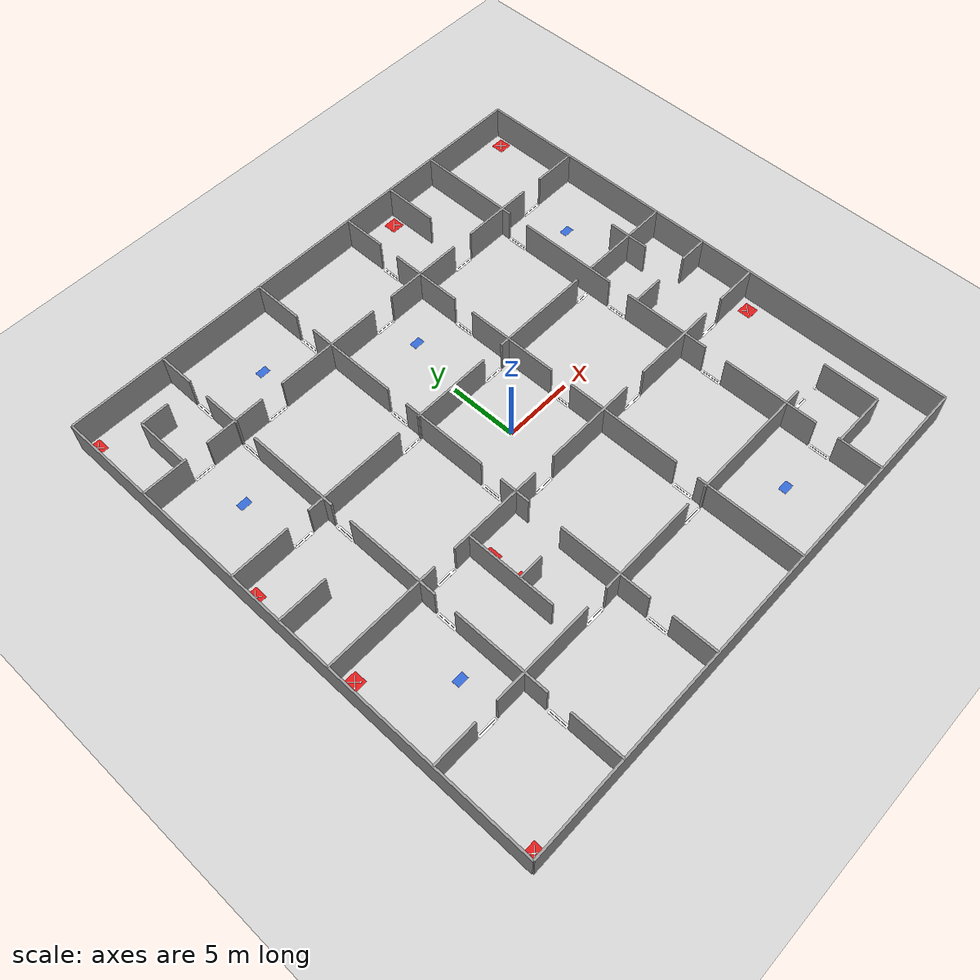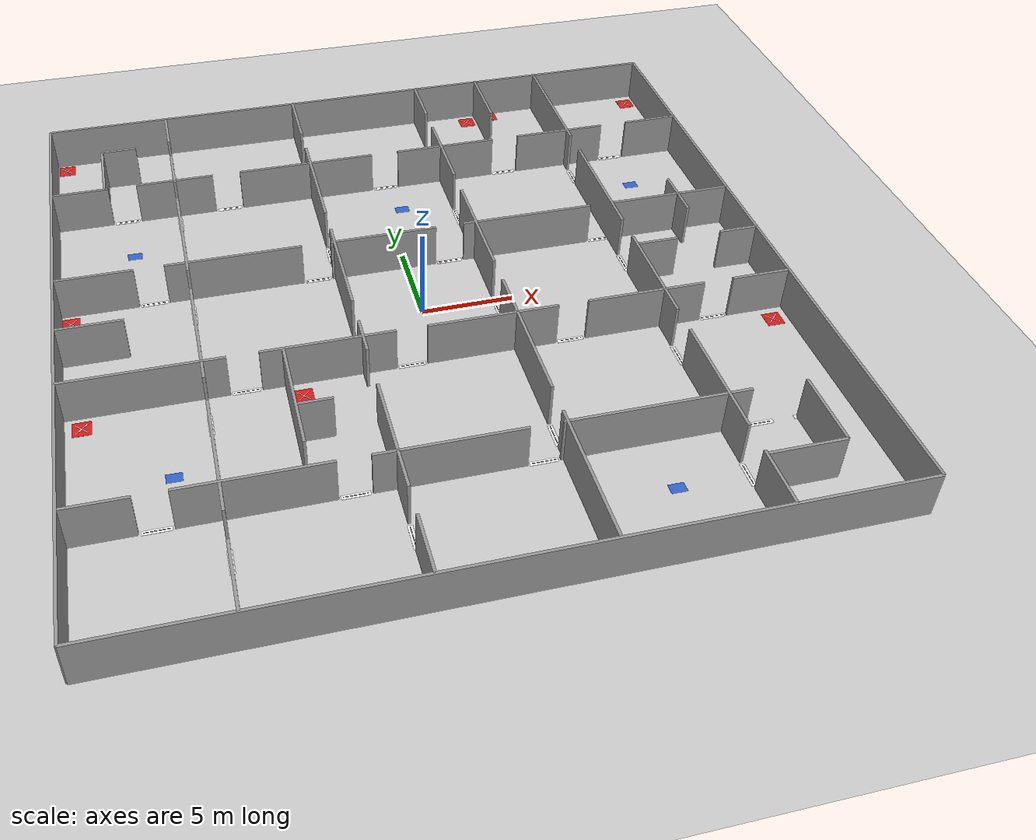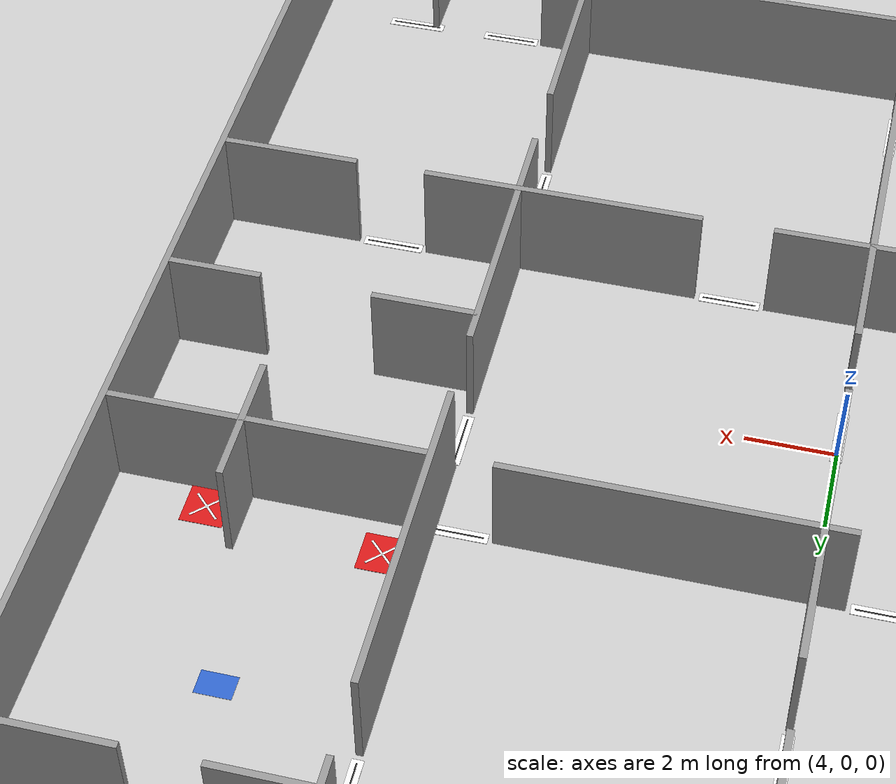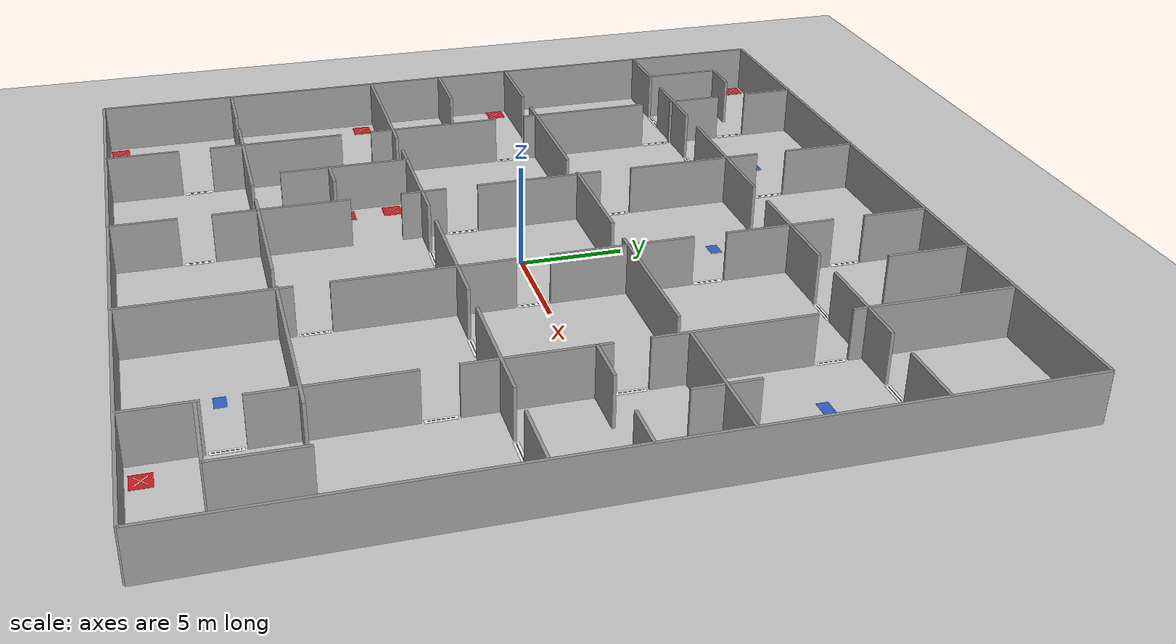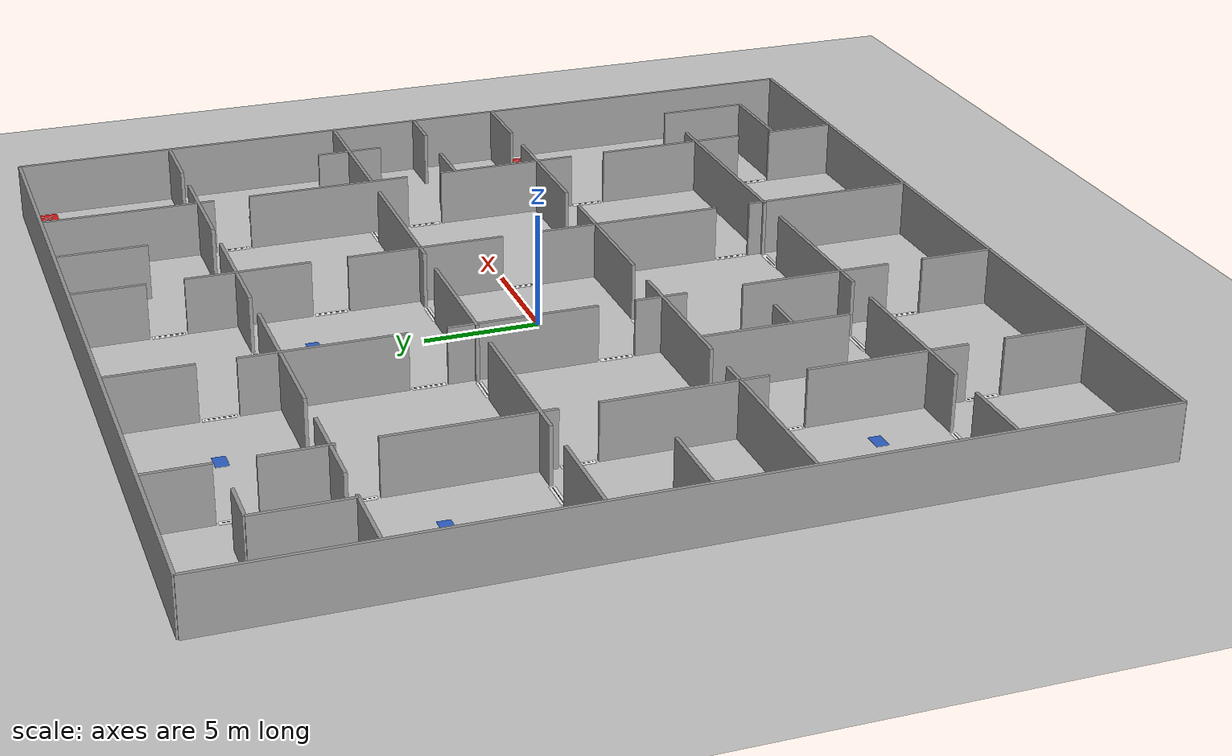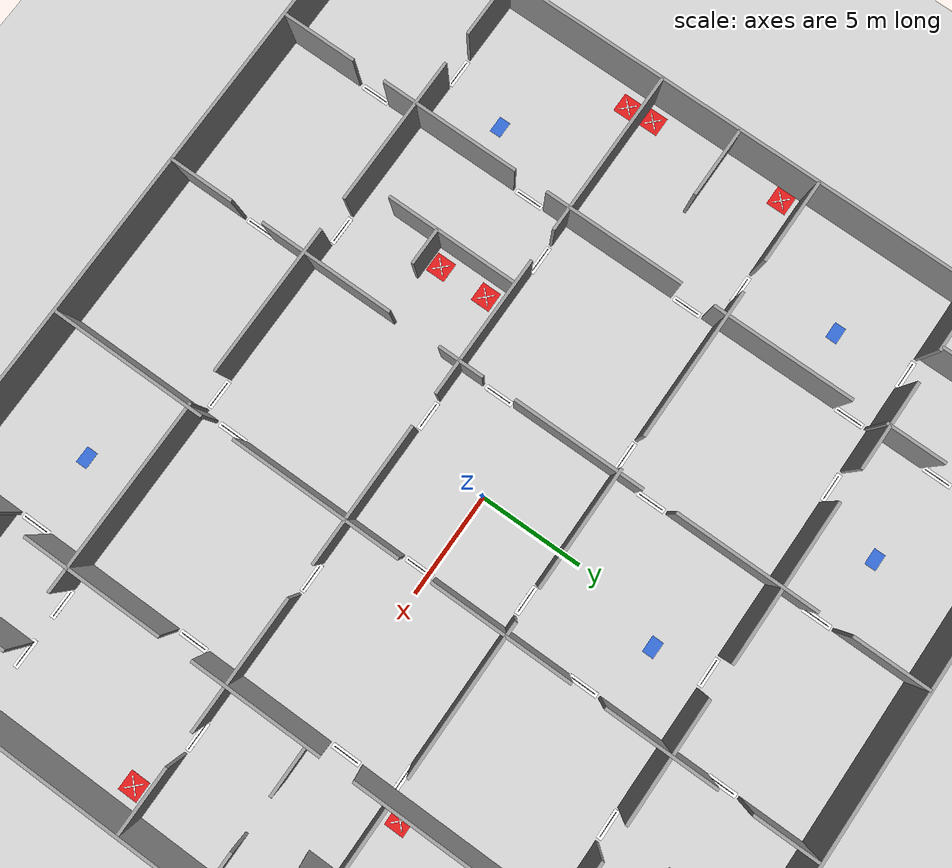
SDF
<sdf version="1.7">
  <world name="default">
    <light name="sun" type="directional">
      <cast_shadows>1</cast_shadows>
      <pose>0 0 10 0 -0 0</pose>
      <diffuse>0.8 0.8 0.8 1</diffuse>
      <specular>0.2 0.2 0.2 1</specular>
      <attenuation>
        <range>1000</range>
        <constant>0.9</constant>
        <linear>0.01</linear>
        <quadratic>0.001</quadratic>
      </attenuation>
      <direction>-0.5 0.1 -0.9</direction>
      <spot>
        <inner_angle>0</inner_angle>
        <outer_angle>0</outer_angle>
        <falloff>0</falloff>
      </spot>
    </light>
    <model name="ground_plane">
      <static>1</static>
      <link name="link">
        <collision name="collision">
          <geometry>
            <plane>
              <normal>0 0 1</normal>
              <size>100 100</size>
            </plane>
          </geometry>
          <surface>
            <friction>
              <ode>
                <mu>100</mu>
                <mu2>50</mu2>
              </ode>
              <torsional>
                <ode />
              </torsional>
            </friction>
            <contact>
              <ode />
            </contact>
            <bounce />
          </surface>
          <max_contacts>10</max_contacts>
        </collision>
        <visual name="visual">
          <cast_shadows>0</cast_shadows>
          <geometry>
            <plane>
              <normal>0 0 1</normal>
              <size>100 100</size>
            </plane>
          </geometry>
          <material>
            <script>
              <uri>file://media/materials/scripts/gazebo.material</uri>
              <name>Gazebo/Grey</name>
            </script>
          </material>
        </visual>
        <self_collide>0</self_collide>
        <enable_wind>0</enable_wind>
        <kinematic>0</kinematic>
      </link>
    </model>
    <gravity>0 0 -9.8</gravity>
    <magnetic_field>6e-06 2.3e-05 -4.2e-05</magnetic_field>
    <atmosphere type="adiabatic" />
    <physics type="ode">
      <max_step_size>0.001</max_step_size>
      <real_time_factor>1</real_time_factor>
      <real_time_update_rate>1000</real_time_update_rate>
    </physics>
    <scene>
      <ambient>0.4 0.4 0.4 1</ambient>
      <background>0.7 0.7 0.7 1</background>
      <shadows>1</shadows>
    </scene>
    <audio>
      <device>default</device>
    </audio>
    <wind />
    <spherical_coordinates>
      <surface_model>EARTH_WGS84</surface_model>
      <latitude_deg>0</latitude_deg>
      <longitude_deg>0</longitude_deg>
      <elevation>0</elevation>
      <heading_deg>0</heading_deg>
    </spherical_coordinates>
    <model name="maze40">
      <pose>0 0 0 0 0 0</pose>
      <static>1</static>
      <link name="Wall_0">
        <collision name="Wall_0_Collision">
          <geometry>
            <box>
              <size>38.000 0.150 2.500</size>
            </box>
          </geometry>
          <pose>0 0 1.250 0 0 0</pose>
          <max_contacts>10</max_contacts>
          <surface>
            <contact>
              <ode />
            </contact>
            <bounce />
            <friction>
              <torsional>
                <ode />
              </torsional>
              <ode />
            </friction>
          </surface>
        </collision>
        <visual name="Wall_0_Visual">
          <pose>0 0 1.250 0 0 0</pose>
          <geometry>
            <box>
              <size>38.000 0.150 2.500</size>
            </box>
          </geometry>
          <material>
            <script>
              <uri>file://media/materials/scripts/gazebo.material</uri>
              <name>Gazebo/Grey</name>
            </script>
            <ambient>1 1 1 1</ambient>
          </material>
          <meta>
            <layer>0</layer>
          </meta>
        </visual>
        <pose>0.000 -19.000 0 0 0 0</pose>
        <self_collide>0</self_collide>
        <enable_wind>0</enable_wind>
        <kinematic>0</kinematic>
      </link>
      <link name="Wall_1">
        <collision name="Wall_1_Collision">
          <geometry>
            <box>
              <size>38.000 0.150 2.500</size>
            </box>
          </geometry>
          <pose>0 0 1.250 0 0 0</pose>
          <max_contacts>10</max_contacts>
          <surface>
            <contact>
              <ode />
            </contact>
            <bounce />
            <friction>
              <torsional>
                <ode />
              </torsional>
              <ode />
            </friction>
          </surface>
        </collision>
        <visual name="Wall_1_Visual">
          <pose>0 0 1.250 0 0 0</pose>
          <geometry>
            <box>
              <size>38.000 0.150 2.500</size>
            </box>
          </geometry>
          <material>
            <script>
              <uri>file://media/materials/scripts/gazebo.material</uri>
              <name>Gazebo/Grey</name>
            </script>
            <ambient>1 1 1 1</ambient>
          </material>
          <meta>
            <layer>0</layer>
          </meta>
        </visual>
        <pose>0.000 19.000 0 0 0 0</pose>
        <self_collide>0</self_collide>
        <enable_wind>0</enable_wind>
        <kinematic>0</kinematic>
      </link>
      <link name="Wall_2">
        <collision name="Wall_2_Collision">
          <geometry>
            <box>
              <size>0.150 38.000 2.500</size>
            </box>
          </geometry>
          <pose>0 0 1.250 0 0 0</pose>
          <max_contacts>10</max_contacts>
          <surface>
            <contact>
              <ode />
            </contact>
            <bounce />
            <friction>
              <torsional>
                <ode />
              </torsional>
              <ode />
            </friction>
          </surface>
        </collision>
        <visual name="Wall_2_Visual">
          <pose>0 0 1.250 0 0 0</pose>
          <geometry>
            <box>
              <size>0.150 38.000 2.500</size>
            </box>
          </geometry>
          <material>
            <script>
              <uri>file://media/materials/scripts/gazebo.material</uri>
              <name>Gazebo/Grey</name>
            </script>
            <ambient>1 1 1 1</ambient>
          </material>
          <meta>
            <layer>0</layer>
          </meta>
        </visual>
        <pose>-19.000 0.000 0 0 0 0</pose>
        <self_collide>0</self_collide>
        <enable_wind>0</enable_wind>
        <kinematic>0</kinematic>
      </link>
      <link name="Wall_3">
        <collision name="Wall_3_Collision">
          <geometry>
            <box>
              <size>0.150 38.000 2.500</size>
            </box>
          </geometry>
          <pose>0 0 1.250 0 0 0</pose>
          <max_contacts>10</max_contacts>
          <surface>
            <contact>
              <ode />
            </contact>
            <bounce />
            <friction>
              <torsional>
                <ode />
              </torsional>
              <ode />
            </friction>
          </surface>
        </collision>
        <visual name="Wall_3_Visual">
          <pose>0 0 1.250 0 0 0</pose>
          <geometry>
            <box>
              <size>0.150 38.000 2.500</size>
            </box>
          </geometry>
          <material>
            <script>
              <uri>file://media/materials/scripts/gazebo.material</uri>
              <name>Gazebo/Grey</name>
            </script>
            <ambient>1 1 1 1</ambient>
          </material>
          <meta>
            <layer>0</layer>
          </meta>
        </visual>
        <pose>19.000 0.000 0 0 0 0</pose>
        <self_collide>0</self_collide>
        <enable_wind>0</enable_wind>
        <kinematic>0</kinematic>
      </link>
      <link name="Wall_4">
        <collision name="Wall_4_Collision">
          <geometry>
            <box>
              <size>0.150 3.700 2.500</size>
            </box>
          </geometry>
          <pose>0 0 1.250 0 0 0</pose>
          <max_contacts>10</max_contacts>
          <surface>
            <contact>
              <ode />
            </contact>
            <bounce />
            <friction>
              <torsional>
                <ode />
              </torsional>
              <ode />
            </friction>
          </surface>
        </collision>
        <visual name="Wall_4_Visual">
          <pose>0 0 1.250 0 0 0</pose>
          <geometry>
            <box>
              <size>0.150 3.700 2.500</size>
            </box>
          </geometry>
          <material>
            <script>
              <uri>file://media/materials/scripts/gazebo.material</uri>
              <name>Gazebo/Grey</name>
            </script>
            <ambient>1 1 1 1</ambient>
          </material>
          <meta>
            <layer>0</layer>
          </meta>
        </visual>
        <pose>-12.000 -17.150 0 0 0 0</pose>
        <self_collide>0</self_collide>
        <enable_wind>0</enable_wind>
        <kinematic>0</kinematic>
      </link>
      <link name="Wall_5">
        <collision name="Wall_5_Collision">
          <geometry>
            <box>
              <size>0.150 6.900 2.500</size>
            </box>
          </geometry>
          <pose>0 0 1.250 0 0 0</pose>
          <max_contacts>10</max_contacts>
          <surface>
            <contact>
              <ode />
            </contact>
            <bounce />
            <friction>
              <torsional>
                <ode />
              </torsional>
              <ode />
            </friction>
          </surface>
        </collision>
        <visual name="Wall_5_Visual">
          <pose>0 0 1.250 0 0 0</pose>
          <geometry>
            <box>
              <size>0.150 6.900 2.500</size>
            </box>
          </geometry>
          <material>
            <script>
              <uri>file://media/materials/scripts/gazebo.material</uri>
              <name>Gazebo/Grey</name>
            </script>
            <ambient>1 1 1 1</ambient>
          </material>
          <meta>
            <layer>0</layer>
          </meta>
        </visual>
        <pose>-12.000 -10.250 0 0 0 0</pose>
        <self_collide>0</self_collide>
        <enable_wind>0</enable_wind>
        <kinematic>0</kinematic>
      </link>
      <link name="Wall_6">
        <collision name="Wall_6_Collision">
          <geometry>
            <box>
              <size>0.150 6.900 2.500</size>
            </box>
          </geometry>
          <pose>0 0 1.250 0 0 0</pose>
          <max_contacts>10</max_contacts>
          <surface>
            <contact>
              <ode />
            </contact>
            <bounce />
            <friction>
              <torsional>
                <ode />
              </torsional>
              <ode />
            </friction>
          </surface>
        </collision>
        <visual name="Wall_6_Visual">
          <pose>0 0 1.250 0 0 0</pose>
          <geometry>
            <box>
              <size>0.150 6.900 2.500</size>
            </box>
          </geometry>
          <material>
            <script>
              <uri>file://media/materials/scripts/gazebo.material</uri>
              <name>Gazebo/Grey</name>
            </script>
            <ambient>1 1 1 1</ambient>
          </material>
          <meta>
            <layer>0</layer>
          </meta>
        </visual>
        <pose>-12.000 -1.750 0 0 0 0</pose>
        <self_collide>0</self_collide>
        <enable_wind>0</enable_wind>
        <kinematic>0</kinematic>
      </link>
      <link name="Wall_7">
        <collision name="Wall_7_Collision">
          <geometry>
            <box>
              <size>0.150 6.900 2.500</size>
            </box>
          </geometry>
          <pose>0 0 1.250 0 0 0</pose>
          <max_contacts>10</max_contacts>
          <surface>
            <contact>
              <ode />
            </contact>
            <bounce />
            <friction>
              <torsional>
                <ode />
              </torsional>
              <ode />
            </friction>
          </surface>
        </collision>
        <visual name="Wall_7_Visual">
          <pose>0 0 1.250 0 0 0</pose>
          <geometry>
            <box>
              <size>0.150 6.900 2.500</size>
            </box>
          </geometry>
          <material>
            <script>
              <uri>file://media/materials/scripts/gazebo.material</uri>
              <name>Gazebo/Grey</name>
            </script>
            <ambient>1 1 1 1</ambient>
          </material>
          <meta>
            <layer>0</layer>
          </meta>
        </visual>
        <pose>-12.000 6.750 0 0 0 0</pose>
        <self_collide>0</self_collide>
        <enable_wind>0</enable_wind>
        <kinematic>0</kinematic>
      </link>
      <link name="Wall_8">
        <collision name="Wall_8_Collision">
          <geometry>
            <box>
              <size>0.150 2.900 2.500</size>
            </box>
          </geometry>
          <pose>0 0 1.250 0 0 0</pose>
          <max_contacts>10</max_contacts>
          <surface>
            <contact>
              <ode />
            </contact>
            <bounce />
            <friction>
              <torsional>
                <ode />
              </torsional>
              <ode />
            </friction>
          </surface>
        </collision>
        <visual name="Wall_8_Visual">
          <pose>0 0 1.250 0 0 0</pose>
          <geometry>
            <box>
              <size>0.150 2.900 2.500</size>
            </box>
          </geometry>
          <material>
            <script>
              <uri>file://media/materials/scripts/gazebo.material</uri>
              <name>Gazebo/Grey</name>
            </script>
            <ambient>1 1 1 1</ambient>
          </material>
          <meta>
            <layer>0</layer>
          </meta>
        </visual>
        <pose>-12.000 13.250 0 0 0 0</pose>
        <self_collide>0</self_collide>
        <enable_wind>0</enable_wind>
        <kinematic>0</kinematic>
      </link>
      <link name="Wall_9">
        <collision name="Wall_9_Collision">
          <geometry>
            <box>
              <size>0.150 2.700 2.500</size>
            </box>
          </geometry>
          <pose>0 0 1.250 0 0 0</pose>
          <max_contacts>10</max_contacts>
          <surface>
            <contact>
              <ode />
            </contact>
            <bounce />
            <friction>
              <torsional>
                <ode />
              </torsional>
              <ode />
            </friction>
          </surface>
        </collision>
        <visual name="Wall_9_Visual">
          <pose>0 0 1.250 0 0 0</pose>
          <geometry>
            <box>
              <size>0.150 2.700 2.500</size>
            </box>
          </geometry>
          <material>
            <script>
              <uri>file://media/materials/scripts/gazebo.material</uri>
              <name>Gazebo/Grey</name>
            </script>
            <ambient>1 1 1 1</ambient>
          </material>
          <meta>
            <layer>0</layer>
          </meta>
        </visual>
        <pose>-12.000 17.650 0 0 0 0</pose>
        <self_collide>0</self_collide>
        <enable_wind>0</enable_wind>
        <kinematic>0</kinematic>
      </link>
      <link name="Wall_10">
        <collision name="Wall_10_Collision">
          <geometry>
            <box>
              <size>0.150 3.200 2.500</size>
            </box>
          </geometry>
          <pose>0 0 1.250 0 0 0</pose>
          <max_contacts>10</max_contacts>
          <surface>
            <contact>
              <ode />
            </contact>
            <bounce />
            <friction>
              <torsional>
                <ode />
              </torsional>
              <ode />
            </friction>
          </surface>
        </collision>
        <visual name="Wall_10_Visual">
          <pose>0 0 1.250 0 0 0</pose>
          <geometry>
            <box>
              <size>0.150 3.200 2.500</size>
            </box>
          </geometry>
          <material>
            <script>
              <uri>file://media/materials/scripts/gazebo.material</uri>
              <name>Gazebo/Grey</name>
            </script>
            <ambient>1 1 1 1</ambient>
          </material>
          <meta>
            <layer>0</layer>
          </meta>
        </visual>
        <pose>-4.000 -17.400 0 0 0 0</pose>
        <self_collide>0</self_collide>
        <enable_wind>0</enable_wind>
        <kinematic>0</kinematic>
      </link>
      <link name="Wall_11">
        <collision name="Wall_11_Collision">
          <geometry>
            <box>
              <size>0.150 6.650 2.500</size>
            </box>
          </geometry>
          <pose>0 0 1.250 0 0 0</pose>
          <max_contacts>10</max_contacts>
          <surface>
            <contact>
              <ode />
            </contact>
            <bounce />
            <friction>
              <torsional>
                <ode />
              </torsional>
              <ode />
            </friction>
          </surface>
        </collision>
        <visual name="Wall_11_Visual">
          <pose>0 0 1.250 0 0 0</pose>
          <geometry>
            <box>
              <size>0.150 6.650 2.500</size>
            </box>
          </geometry>
          <material>
            <script>
              <uri>file://media/materials/scripts/gazebo.material</uri>
              <name>Gazebo/Grey</name>
            </script>
            <ambient>1 1 1 1</ambient>
          </material>
          <meta>
            <layer>0</layer>
          </meta>
        </visual>
        <pose>-4.000 -10.875 0 0 0 0</pose>
        <self_collide>0</self_collide>
        <enable_wind>0</enable_wind>
        <kinematic>0</kinematic>
      </link>
      <link name="Wall_11b">
        <collision name="Wall_11b_Collision">
          <geometry>
            <box>
              <size>0.150 2.250 2.500</size>
            </box>
          </geometry>
          <pose>0 0 1.250 0 0 0</pose>
          <max_contacts>10</max_contacts>
          <surface>
            <contact>
              <ode />
            </contact>
            <bounce />
            <friction>
              <torsional>
                <ode />
              </torsional>
              <ode />
            </friction>
          </surface>
        </collision>
        <visual name="Wall_11b_Visual">
          <pose>0 0 1.250 0 0 0</pose>
          <geometry>
            <box>
              <size>0.150 2.250 2.500</size>
            </box>
          </geometry>
          <material>
            <script>
              <uri>file://media/materials/scripts/gazebo.material</uri>
              <name>Gazebo/Grey</name>
            </script>
            <ambient>1 1 1 1</ambient>
          </material>
          <meta>
            <layer>0</layer>
          </meta>
        </visual>
        <pose>-4.000 -3.925 0 0 0 0</pose>
        <self_collide>0</self_collide>
        <enable_wind>0</enable_wind>
        <kinematic>0</kinematic>
      </link>
      <link name="Wall_12">
        <collision name="Wall_12_Collision">
          <geometry>
            <box>
              <size>0.150 6.400 2.500</size>
            </box>
          </geometry>
          <pose>0 0 1.250 0 0 0</pose>
          <max_contacts>10</max_contacts>
          <surface>
            <contact>
              <ode />
            </contact>
            <bounce />
            <friction>
              <torsional>
                <ode />
              </torsional>
              <ode />
            </friction>
          </surface>
        </collision>
        <visual name="Wall_12_Visual">
          <pose>0 0 1.250 0 0 0</pose>
          <geometry>
            <box>
              <size>0.150 6.400 2.500</size>
            </box>
          </geometry>
          <material>
            <script>
              <uri>file://media/materials/scripts/gazebo.material</uri>
              <name>Gazebo/Grey</name>
            </script>
            <ambient>1 1 1 1</ambient>
          </material>
          <meta>
            <layer>0</layer>
          </meta>
        </visual>
        <pose>-4.000 2.000 0 0 0 0</pose>
        <self_collide>0</self_collide>
        <enable_wind>0</enable_wind>
        <kinematic>0</kinematic>
      </link>
      <link name="Wall_13">
        <collision name="Wall_13_Collision">
          <geometry>
            <box>
              <size>0.150 6.900 2.500</size>
            </box>
          </geometry>
          <pose>0 0 1.250 0 0 0</pose>
          <max_contacts>10</max_contacts>
          <surface>
            <contact>
              <ode />
            </contact>
            <bounce />
            <friction>
              <torsional>
                <ode />
              </torsional>
              <ode />
            </friction>
          </surface>
        </collision>
        <visual name="Wall_13_Visual">
          <pose>0 0 1.250 0 0 0</pose>
          <geometry>
            <box>
              <size>0.150 6.900 2.500</size>
            </box>
          </geometry>
          <material>
            <script>
              <uri>file://media/materials/scripts/gazebo.material</uri>
              <name>Gazebo/Grey</name>
            </script>
            <ambient>1 1 1 1</ambient>
          </material>
          <meta>
            <layer>0</layer>
          </meta>
        </visual>
        <pose>-4.000 10.250 0 0 0 0</pose>
        <self_collide>0</self_collide>
        <enable_wind>0</enable_wind>
        <kinematic>0</kinematic>
      </link>
      <link name="Wall_14">
        <collision name="Wall_14_Collision">
          <geometry>
            <box>
              <size>0.150 3.700 2.500</size>
            </box>
          </geometry>
          <pose>0 0 1.250 0 0 0</pose>
          <max_contacts>10</max_contacts>
          <surface>
            <contact>
              <ode />
            </contact>
            <bounce />
            <friction>
              <torsional>
                <ode />
              </torsional>
              <ode />
            </friction>
          </surface>
        </collision>
        <visual name="Wall_14_Visual">
          <pose>0 0 1.250 0 0 0</pose>
          <geometry>
            <box>
              <size>0.150 3.700 2.500</size>
            </box>
          </geometry>
          <material>
            <script>
              <uri>file://media/materials/scripts/gazebo.material</uri>
              <name>Gazebo/Grey</name>
            </script>
            <ambient>1 1 1 1</ambient>
          </material>
          <meta>
            <layer>0</layer>
          </meta>
        </visual>
        <pose>-4.000 17.150 0 0 0 0</pose>
        <self_collide>0</self_collide>
        <enable_wind>0</enable_wind>
        <kinematic>0</kinematic>
      </link>
      <link name="Wall_15">
        <collision name="Wall_15_Collision">
          <geometry>
            <box>
              <size>0.150 7.700 2.500</size>
            </box>
          </geometry>
          <pose>0 0 1.250 0 0 0</pose>
          <max_contacts>10</max_contacts>
          <surface>
            <contact>
              <ode />
            </contact>
            <bounce />
            <friction>
              <torsional>
                <ode />
              </torsional>
              <ode />
            </friction>
          </surface>
        </collision>
        <visual name="Wall_15_Visual">
          <pose>0 0 1.250 0 0 0</pose>
          <geometry>
            <box>
              <size>0.150 7.700 2.500</size>
            </box>
          </geometry>
          <material>
            <script>
              <uri>file://media/materials/scripts/gazebo.material</uri>
              <name>Gazebo/Grey</name>
            </script>
            <ambient>1 1 1 1</ambient>
          </material>
          <meta>
            <layer>0</layer>
          </meta>
        </visual>
        <pose>4.000 -15.150 0 0 0 0</pose>
        <self_collide>0</self_collide>
        <enable_wind>0</enable_wind>
        <kinematic>0</kinematic>
      </link>
      <link name="Wall_16">
        <collision name="Wall_16_Collision">
          <geometry>
            <box>
              <size>0.150 8.400 2.500</size>
            </box>
          </geometry>
          <pose>0 0 1.250 0 0 0</pose>
          <max_contacts>10</max_contacts>
          <surface>
            <contact>
              <ode />
            </contact>
            <bounce />
            <friction>
              <torsional>
                <ode />
              </torsional>
              <ode />
            </friction>
          </surface>
        </collision>
        <visual name="Wall_16_Visual">
          <pose>0 0 1.250 0 0 0</pose>
          <geometry>
            <box>
              <size>0.150 8.400 2.500</size>
            </box>
          </geometry>
          <material>
            <script>
              <uri>file://media/materials/scripts/gazebo.material</uri>
              <name>Gazebo/Grey</name>
            </script>
            <ambient>1 1 1 1</ambient>
          </material>
          <meta>
            <layer>0</layer>
          </meta>
        </visual>
        <pose>4.000 -5.500 0 0 0 0</pose>
        <self_collide>0</self_collide>
        <enable_wind>0</enable_wind>
        <kinematic>0</kinematic>
      </link>
      <link name="Wall_17">
        <collision name="Wall_17_Collision">
          <geometry>
            <box>
              <size>0.150 6.900 2.500</size>
            </box>
          </geometry>
          <pose>0 0 1.250 0 0 0</pose>
          <max_contacts>10</max_contacts>
          <surface>
            <contact>
              <ode />
            </contact>
            <bounce />
            <friction>
              <torsional>
                <ode />
              </torsional>
              <ode />
            </friction>
          </surface>
        </collision>
        <visual name="Wall_17_Visual">
          <pose>0 0 1.250 0 0 0</pose>
          <geometry>
            <box>
              <size>0.150 6.900 2.500</size>
            </box>
          </geometry>
          <material>
            <script>
              <uri>file://media/materials/scripts/gazebo.material</uri>
              <name>Gazebo/Grey</name>
            </script>
            <ambient>1 1 1 1</ambient>
          </material>
          <meta>
            <layer>0</layer>
          </meta>
        </visual>
        <pose>4.000 3.750 0 0 0 0</pose>
        <self_collide>0</self_collide>
        <enable_wind>0</enable_wind>
        <kinematic>0</kinematic>
      </link>
      <link name="Wall_18">
        <collision name="Wall_18_Collision">
          <geometry>
            <box>
              <size>0.150 5.400 2.500</size>
            </box>
          </geometry>
          <pose>0 0 1.250 0 0 0</pose>
          <max_contacts>10</max_contacts>
          <surface>
            <contact>
              <ode />
            </contact>
            <bounce />
            <friction>
              <torsional>
                <ode />
              </torsional>
              <ode />
            </friction>
          </surface>
        </collision>
        <visual name="Wall_18_Visual">
          <pose>0 0 1.250 0 0 0</pose>
          <geometry>
            <box>
              <size>0.150 5.400 2.500</size>
            </box>
          </geometry>
          <material>
            <script>
              <uri>file://media/materials/scripts/gazebo.material</uri>
              <name>Gazebo/Grey</name>
            </script>
            <ambient>1 1 1 1</ambient>
          </material>
          <meta>
            <layer>0</layer>
          </meta>
        </visual>
        <pose>4.000 11.500 0 0 0 0</pose>
        <self_collide>0</self_collide>
        <enable_wind>0</enable_wind>
        <kinematic>0</kinematic>
      </link>
      <link name="Wall_19">
        <collision name="Wall_19_Collision">
          <geometry>
            <box>
              <size>0.150 3.200 2.500</size>
            </box>
          </geometry>
          <pose>0 0 1.250 0 0 0</pose>
          <max_contacts>10</max_contacts>
          <surface>
            <contact>
              <ode />
            </contact>
            <bounce />
            <friction>
              <torsional>
                <ode />
              </torsional>
              <ode />
            </friction>
          </surface>
        </collision>
        <visual name="Wall_19_Visual">
          <pose>0 0 1.250 0 0 0</pose>
          <geometry>
            <box>
              <size>0.150 3.200 2.500</size>
            </box>
          </geometry>
          <material>
            <script>
              <uri>file://media/materials/scripts/gazebo.material</uri>
              <name>Gazebo/Grey</name>
            </script>
            <ambient>1 1 1 1</ambient>
          </material>
          <meta>
            <layer>0</layer>
          </meta>
        </visual>
        <pose>4.000 17.400 0 0 0 0</pose>
        <self_collide>0</self_collide>
        <enable_wind>0</enable_wind>
        <kinematic>0</kinematic>
      </link>
      <link name="Wall_20">
        <collision name="Wall_20_Collision">
          <geometry>
            <box>
              <size>0.150 3.200 2.500</size>
            </box>
          </geometry>
          <pose>0 0 1.250 0 0 0</pose>
          <max_contacts>10</max_contacts>
          <surface>
            <contact>
              <ode />
            </contact>
            <bounce />
            <friction>
              <torsional>
                <ode />
              </torsional>
              <ode />
            </friction>
          </surface>
        </collision>
        <visual name="Wall_20_Visual">
          <pose>0 0 1.250 0 0 0</pose>
          <geometry>
            <box>
              <size>0.150 3.200 2.500</size>
            </box>
          </geometry>
          <material>
            <script>
              <uri>file://media/materials/scripts/gazebo.material</uri>
              <name>Gazebo/Grey</name>
            </script>
            <ambient>1 1 1 1</ambient>
          </material>
          <meta>
            <layer>0</layer>
          </meta>
        </visual>
        <pose>12.000 -17.400 0 0 0 0</pose>
        <self_collide>0</self_collide>
        <enable_wind>0</enable_wind>
        <kinematic>0</kinematic>
      </link>
      <link name="Wall_21">
        <collision name="Wall_21_Collision">
          <geometry>
            <box>
              <size>0.150 6.900 2.500</size>
            </box>
          </geometry>
          <pose>0 0 1.250 0 0 0</pose>
          <max_contacts>10</max_contacts>
          <surface>
            <contact>
              <ode />
            </contact>
            <bounce />
            <friction>
              <torsional>
                <ode />
              </torsional>
              <ode />
            </friction>
          </surface>
        </collision>
        <visual name="Wall_21_Visual">
          <pose>0 0 1.250 0 0 0</pose>
          <geometry>
            <box>
              <size>0.150 6.900 2.500</size>
            </box>
          </geometry>
          <material>
            <script>
              <uri>file://media/materials/scripts/gazebo.material</uri>
              <name>Gazebo/Grey</name>
            </script>
            <ambient>1 1 1 1</ambient>
          </material>
          <meta>
            <layer>0</layer>
          </meta>
        </visual>
        <pose>12.000 -10.750 0 0 0 0</pose>
        <self_collide>0</self_collide>
        <enable_wind>0</enable_wind>
        <kinematic>0</kinematic>
      </link>
      <link name="Wall_22">
        <collision name="Wall_22_Collision">
          <geometry>
            <box>
              <size>0.150 6.400 2.500</size>
            </box>
          </geometry>
          <pose>0 0 1.250 0 0 0</pose>
          <max_contacts>10</max_contacts>
          <surface>
            <contact>
              <ode />
            </contact>
            <bounce />
            <friction>
              <torsional>
                <ode />
              </torsional>
              <ode />
            </friction>
          </surface>
        </collision>
        <visual name="Wall_22_Visual">
          <pose>0 0 1.250 0 0 0</pose>
          <geometry>
            <box>
              <size>0.150 6.400 2.500</size>
            </box>
          </geometry>
          <material>
            <script>
              <uri>file://media/materials/scripts/gazebo.material</uri>
              <name>Gazebo/Grey</name>
            </script>
            <ambient>1 1 1 1</ambient>
          </material>
          <meta>
            <layer>0</layer>
          </meta>
        </visual>
        <pose>12.000 -2.500 0 0 0 0</pose>
        <self_collide>0</self_collide>
        <enable_wind>0</enable_wind>
        <kinematic>0</kinematic>
      </link>
      <link name="Wall_23">
        <collision name="Wall_23_Collision">
          <geometry>
            <box>
              <size>0.150 7.400 2.500</size>
            </box>
          </geometry>
          <pose>0 0 1.250 0 0 0</pose>
          <max_contacts>10</max_contacts>
          <surface>
            <contact>
              <ode />
            </contact>
            <bounce />
            <friction>
              <torsional>
                <ode />
              </torsional>
              <ode />
            </friction>
          </surface>
        </collision>
        <visual name="Wall_23_Visual">
          <pose>0 0 1.250 0 0 0</pose>
          <geometry>
            <box>
              <size>0.150 7.400 2.500</size>
            </box>
          </geometry>
          <material>
            <script>
              <uri>file://media/materials/scripts/gazebo.material</uri>
              <name>Gazebo/Grey</name>
            </script>
            <ambient>1 1 1 1</ambient>
          </material>
          <meta>
            <layer>0</layer>
          </meta>
        </visual>
        <pose>12.000 6.000 0 0 0 0</pose>
        <self_collide>0</self_collide>
        <enable_wind>0</enable_wind>
        <kinematic>0</kinematic>
      </link>
      <link name="Wall_24">
        <collision name="Wall_24_Collision">
          <geometry>
            <box>
              <size>0.150 7.700 2.500</size>
            </box>
          </geometry>
          <pose>0 0 1.250 0 0 0</pose>
          <max_contacts>10</max_contacts>
          <surface>
            <contact>
              <ode />
            </contact>
            <bounce />
            <friction>
              <torsional>
                <ode />
              </torsional>
              <ode />
            </friction>
          </surface>
        </collision>
        <visual name="Wall_24_Visual">
          <pose>0 0 1.250 0 0 0</pose>
          <geometry>
            <box>
              <size>0.150 7.700 2.500</size>
            </box>
          </geometry>
          <material>
            <script>
              <uri>file://media/materials/scripts/gazebo.material</uri>
              <name>Gazebo/Grey</name>
            </script>
            <ambient>1 1 1 1</ambient>
          </material>
          <meta>
            <layer>0</layer>
          </meta>
        </visual>
        <pose>12.000 15.150 0 0 0 0</pose>
        <self_collide>0</self_collide>
        <enable_wind>0</enable_wind>
        <kinematic>0</kinematic>
      </link>
      <link name="Wall_25">
        <collision name="Wall_25_Collision">
          <geometry>
            <box>
              <size>3.200 0.150 2.500</size>
            </box>
          </geometry>
          <pose>0 0 1.250 0 0 0</pose>
          <max_contacts>10</max_contacts>
          <surface>
            <contact>
              <ode />
            </contact>
            <bounce />
            <friction>
              <torsional>
                <ode />
              </torsional>
              <ode />
            </friction>
          </surface>
        </collision>
        <visual name="Wall_25_Visual">
          <pose>0 0 1.250 0 0 0</pose>
          <geometry>
            <box>
              <size>3.200 0.150 2.500</size>
            </box>
          </geometry>
          <material>
            <script>
              <uri>file://media/materials/scripts/gazebo.material</uri>
              <name>Gazebo/Grey</name>
            </script>
            <ambient>1 1 1 1</ambient>
          </material>
          <meta>
            <layer>0</layer>
          </meta>
        </visual>
        <pose>-17.400 -12.000 0 0 0 0</pose>
        <self_collide>0</self_collide>
        <enable_wind>0</enable_wind>
        <kinematic>0</kinematic>
      </link>
      <link name="Wall_26">
        <collision name="Wall_26_Collision">
          <geometry>
            <box>
              <size>7.400 0.150 2.500</size>
            </box>
          </geometry>
          <pose>0 0 1.250 0 0 0</pose>
          <max_contacts>10</max_contacts>
          <surface>
            <contact>
              <ode />
            </contact>
            <bounce />
            <friction>
              <torsional>
                <ode />
              </torsional>
              <ode />
            </friction>
          </surface>
        </collision>
        <visual name="Wall_26_Visual">
          <pose>0 0 1.250 0 0 0</pose>
          <geometry>
            <box>
              <size>7.400 0.150 2.500</size>
            </box>
          </geometry>
          <material>
            <script>
              <uri>file://media/materials/scripts/gazebo.material</uri>
              <name>Gazebo/Grey</name>
            </script>
            <ambient>1 1 1 1</ambient>
          </material>
          <meta>
            <layer>0</layer>
          </meta>
        </visual>
        <pose>-10.500 -12.000 0 0 0 0</pose>
        <self_collide>0</self_collide>
        <enable_wind>0</enable_wind>
        <kinematic>0</kinematic>
      </link>
      <link name="Wall_27">
        <collision name="Wall_27_Collision">
          <geometry>
            <box>
              <size>7.400 0.150 2.500</size>
            </box>
          </geometry>
          <pose>0 0 1.250 0 0 0</pose>
          <max_contacts>10</max_contacts>
          <surface>
            <contact>
              <ode />
            </contact>
            <bounce />
            <friction>
              <torsional>
                <ode />
              </torsional>
              <ode />
            </friction>
          </surface>
        </collision>
        <visual name="Wall_27_Visual">
          <pose>0 0 1.250 0 0 0</pose>
          <geometry>
            <box>
              <size>7.400 0.150 2.500</size>
            </box>
          </geometry>
          <material>
            <script>
              <uri>file://media/materials/scripts/gazebo.material</uri>
              <name>Gazebo/Grey</name>
            </script>
            <ambient>1 1 1 1</ambient>
          </material>
          <meta>
            <layer>0</layer>
          </meta>
        </visual>
        <pose>-1.500 -12.000 0 0 0 0</pose>
        <self_collide>0</self_collide>
        <enable_wind>0</enable_wind>
        <kinematic>0</kinematic>
      </link>
      <link name="Wall_28">
        <collision name="Wall_28_Collision">
          <geometry>
            <box>
              <size>9.400 0.150 2.500</size>
            </box>
          </geometry>
          <pose>0 0 1.250 0 0 0</pose>
          <max_contacts>10</max_contacts>
          <surface>
            <contact>
              <ode />
            </contact>
            <bounce />
            <friction>
              <torsional>
                <ode />
              </torsional>
              <ode />
            </friction>
          </surface>
        </collision>
        <visual name="Wall_28_Visual">
          <pose>0 0 1.250 0 0 0</pose>
          <geometry>
            <box>
              <size>9.400 0.150 2.500</size>
            </box>
          </geometry>
          <material>
            <script>
              <uri>file://media/materials/scripts/gazebo.material</uri>
              <name>Gazebo/Grey</name>
            </script>
            <ambient>1 1 1 1</ambient>
          </material>
          <meta>
            <layer>0</layer>
          </meta>
        </visual>
        <pose>8.500 -12.000 0 0 0 0</pose>
        <self_collide>0</self_collide>
        <enable_wind>0</enable_wind>
        <kinematic>0</kinematic>
      </link>
      <link name="Wall_31">
        <collision name="Wall_31_Collision">
          <geometry>
            <box>
              <size>8.200 0.150 2.500</size>
            </box>
          </geometry>
          <pose>0 0 1.250 0 0 0</pose>
          <max_contacts>10</max_contacts>
          <surface>
            <contact>
              <ode />
            </contact>
            <bounce />
            <friction>
              <torsional>
                <ode />
              </torsional>
              <ode />
            </friction>
          </surface>
        </collision>
        <visual name="Wall_31_Visual">
          <pose>0 0 1.250 0 0 0</pose>
          <geometry>
            <box>
              <size>8.200 0.150 2.500</size>
            </box>
          </geometry>
          <material>
            <script>
              <uri>file://media/materials/scripts/gazebo.material</uri>
              <name>Gazebo/Grey</name>
            </script>
            <ambient>1 1 1 1</ambient>
          </material>
          <meta>
            <layer>0</layer>
          </meta>
        </visual>
        <pose>-14.900 -4.000 0 0 0 0</pose>
        <self_collide>0</self_collide>
        <enable_wind>0</enable_wind>
        <kinematic>0</kinematic>
      </link>
      <link name="Wall_32">
        <collision name="Wall_32_Collision">
          <geometry>
            <box>
              <size>6.900 0.150 2.500</size>
            </box>
          </geometry>
          <pose>0 0 1.250 0 0 0</pose>
          <max_contacts>10</max_contacts>
          <surface>
            <contact>
              <ode />
            </contact>
            <bounce />
            <friction>
              <torsional>
                <ode />
              </torsional>
              <ode />
            </friction>
          </surface>
        </collision>
        <visual name="Wall_32_Visual">
          <pose>0 0 1.250 0 0 0</pose>
          <geometry>
            <box>
              <size>6.900 0.150 2.500</size>
            </box>
          </geometry>
          <material>
            <script>
              <uri>file://media/materials/scripts/gazebo.material</uri>
              <name>Gazebo/Grey</name>
            </script>
            <ambient>1 1 1 1</ambient>
          </material>
          <meta>
            <layer>0</layer>
          </meta>
        </visual>
        <pose>-5.750 -4.000 0 0 0 0</pose>
        <self_collide>0</self_collide>
        <enable_wind>0</enable_wind>
        <kinematic>0</kinematic>
      </link>
      <link name="Wall_33">
        <collision name="Wall_33_Collision">
          <geometry>
            <box>
              <size>6.900 0.150 2.500</size>
            </box>
          </geometry>
          <pose>0 0 1.250 0 0 0</pose>
          <max_contacts>10</max_contacts>
          <surface>
            <contact>
              <ode />
            </contact>
            <bounce />
            <friction>
              <torsional>
                <ode />
              </torsional>
              <ode />
            </friction>
          </surface>
        </collision>
        <visual name="Wall_33_Visual">
          <pose>0 0 1.250 0 0 0</pose>
          <geometry>
            <box>
              <size>6.900 0.150 2.500</size>
            </box>
          </geometry>
          <material>
            <script>
              <uri>file://media/materials/scripts/gazebo.material</uri>
              <name>Gazebo/Grey</name>
            </script>
            <ambient>1 1 1 1</ambient>
          </material>
          <meta>
            <layer>0</layer>
          </meta>
        </visual>
        <pose>2.750 -4.000 0 0 0 0</pose>
        <self_collide>0</self_collide>
        <enable_wind>0</enable_wind>
        <kinematic>0</kinematic>
      </link>
      <link name="Wall_34">
        <collision name="Wall_34_Collision">
          <geometry>
            <box>
              <size>6.400 0.150 2.500</size>
            </box>
          </geometry>
          <pose>0 0 1.250 0 0 0</pose>
          <max_contacts>10</max_contacts>
          <surface>
            <contact>
              <ode />
            </contact>
            <bounce />
            <friction>
              <torsional>
                <ode />
              </torsional>
              <ode />
            </friction>
          </surface>
        </collision>
        <visual name="Wall_34_Visual">
          <pose>0 0 1.250 0 0 0</pose>
          <geometry>
            <box>
              <size>6.400 0.150 2.500</size>
            </box>
          </geometry>
          <material>
            <script>
              <uri>file://media/materials/scripts/gazebo.material</uri>
              <name>Gazebo/Grey</name>
            </script>
            <ambient>1 1 1 1</ambient>
          </material>
          <meta>
            <layer>0</layer>
          </meta>
        </visual>
        <pose>11.000 -4.000 0 0 0 0</pose>
        <self_collide>0</self_collide>
        <enable_wind>0</enable_wind>
        <kinematic>0</kinematic>
      </link>
      <link name="Wall_35">
        <collision name="Wall_35_Collision">
          <geometry>
            <box>
              <size>3.200 0.150 2.500</size>
            </box>
          </geometry>
          <pose>0 0 1.250 0 0 0</pose>
          <max_contacts>10</max_contacts>
          <surface>
            <contact>
              <ode />
            </contact>
            <bounce />
            <friction>
              <torsional>
                <ode />
              </torsional>
              <ode />
            </friction>
          </surface>
        </collision>
        <visual name="Wall_35_Visual">
          <pose>0 0 1.250 0 0 0</pose>
          <geometry>
            <box>
              <size>3.200 0.150 2.500</size>
            </box>
          </geometry>
          <material>
            <script>
              <uri>file://media/materials/scripts/gazebo.material</uri>
              <name>Gazebo/Grey</name>
            </script>
            <ambient>1 1 1 1</ambient>
          </material>
          <meta>
            <layer>0</layer>
          </meta>
        </visual>
        <pose>17.400 -4.000 0 0 0 0</pose>
        <self_collide>0</self_collide>
        <enable_wind>0</enable_wind>
        <kinematic>0</kinematic>
      </link>
      <link name="Wall_36">
        <collision name="Wall_36_Collision">
          <geometry>
            <box>
              <size>4.200 0.150 2.500</size>
            </box>
          </geometry>
          <pose>0 0 1.250 0 0 0</pose>
          <max_contacts>10</max_contacts>
          <surface>
            <contact>
              <ode />
            </contact>
            <bounce />
            <friction>
              <torsional>
                <ode />
              </torsional>
              <ode />
            </friction>
          </surface>
        </collision>
        <visual name="Wall_36_Visual">
          <pose>0 0 1.250 0 0 0</pose>
          <geometry>
            <box>
              <size>4.200 0.150 2.500</size>
            </box>
          </geometry>
          <material>
            <script>
              <uri>file://media/materials/scripts/gazebo.material</uri>
              <name>Gazebo/Grey</name>
            </script>
            <ambient>1 1 1 1</ambient>
          </material>
          <meta>
            <layer>0</layer>
          </meta>
        </visual>
        <pose>-16.900 4.000 0 0 0 0</pose>
        <self_collide>0</self_collide>
        <enable_wind>0</enable_wind>
        <kinematic>0</kinematic>
      </link>
      <link name="Wall_37">
        <collision name="Wall_37_Collision">
          <geometry>
            <box>
              <size>7.400 0.150 2.500</size>
            </box>
          </geometry>
          <pose>0 0 1.250 0 0 0</pose>
          <max_contacts>10</max_contacts>
          <surface>
            <contact>
              <ode />
            </contact>
            <bounce />
            <friction>
              <torsional>
                <ode />
              </torsional>
              <ode />
            </friction>
          </surface>
        </collision>
        <visual name="Wall_37_Visual">
          <pose>0 0 1.250 0 0 0</pose>
          <geometry>
            <box>
              <size>7.400 0.150 2.500</size>
            </box>
          </geometry>
          <material>
            <script>
              <uri>file://media/materials/scripts/gazebo.material</uri>
              <name>Gazebo/Grey</name>
            </script>
            <ambient>1 1 1 1</ambient>
          </material>
          <meta>
            <layer>0</layer>
          </meta>
        </visual>
        <pose>-9.500 4.000 0 0 0 0</pose>
        <self_collide>0</self_collide>
        <enable_wind>0</enable_wind>
        <kinematic>0</kinematic>
      </link>
      <link name="Wall_38">
        <collision name="Wall_38_Collision">
          <geometry>
            <box>
              <size>5.900 0.150 2.500</size>
            </box>
          </geometry>
          <pose>0 0 1.250 0 0 0</pose>
          <max_contacts>10</max_contacts>
          <surface>
            <contact>
              <ode />
            </contact>
            <bounce />
            <friction>
              <torsional>
                <ode />
              </torsional>
              <ode />
            </friction>
          </surface>
        </collision>
        <visual name="Wall_38_Visual">
          <pose>0 0 1.250 0 0 0</pose>
          <geometry>
            <box>
              <size>5.900 0.150 2.500</size>
            </box>
          </geometry>
          <material>
            <script>
              <uri>file://media/materials/scripts/gazebo.material</uri>
              <name>Gazebo/Grey</name>
            </script>
            <ambient>1 1 1 1</ambient>
          </material>
          <meta>
            <layer>0</layer>
          </meta>
        </visual>
        <pose>-1.250 4.000 0 0 0 0</pose>
        <self_collide>0</self_collide>
        <enable_wind>0</enable_wind>
        <kinematic>0</kinematic>
      </link>
      <link name="Wall_39">
        <collision name="Wall_39_Collision">
          <geometry>
            <box>
              <size>7.400 0.150 2.500</size>
            </box>
          </geometry>
          <pose>0 0 1.250 0 0 0</pose>
          <max_contacts>10</max_contacts>
          <surface>
            <contact>
              <ode />
            </contact>
            <bounce />
            <friction>
              <torsional>
                <ode />
              </torsional>
              <ode />
            </friction>
          </surface>
        </collision>
        <visual name="Wall_39_Visual">
          <pose>0 0 1.250 0 0 0</pose>
          <geometry>
            <box>
              <size>7.400 0.150 2.500</size>
            </box>
          </geometry>
          <material>
            <script>
              <uri>file://media/materials/scripts/gazebo.material</uri>
              <name>Gazebo/Grey</name>
            </script>
            <ambient>1 1 1 1</ambient>
          </material>
          <meta>
            <layer>0</layer>
          </meta>
        </visual>
        <pose>7.000 4.000 0 0 0 0</pose>
        <self_collide>0</self_collide>
        <enable_wind>0</enable_wind>
        <kinematic>0</kinematic>
      </link>
      <link name="Wall_40">
        <collision name="Wall_40_Collision">
          <geometry>
            <box>
              <size>6.925 0.150 2.500</size>
            </box>
          </geometry>
          <pose>0 0 1.250 0 0 0</pose>
          <max_contacts>10</max_contacts>
          <surface>
            <contact>
              <ode />
            </contact>
            <bounce />
            <friction>
              <torsional>
                <ode />
              </torsional>
              <ode />
            </friction>
          </surface>
        </collision>
        <visual name="Wall_40_Visual">
          <pose>0 0 1.250 0 0 0</pose>
          <geometry>
            <box>
              <size>6.925 0.150 2.500</size>
            </box>
          </geometry>
          <material>
            <script>
              <uri>file://media/materials/scripts/gazebo.material</uri>
              <name>Gazebo/Grey</name>
            </script>
            <ambient>1 1 1 1</ambient>
          </material>
          <meta>
            <layer>0</layer>
          </meta>
        </visual>
        <pose>15.5375 4.000 0 0 0 0</pose>
        <self_collide>0</self_collide>
        <enable_wind>0</enable_wind>
        <kinematic>0</kinematic>
      </link>
      <link name="Wall_41">
        <collision name="Wall_41_Collision">
          <geometry>
            <box>
              <size>3.200 0.150 2.500</size>
            </box>
          </geometry>
          <pose>0 0 1.250 0 0 0</pose>
          <max_contacts>10</max_contacts>
          <surface>
            <contact>
              <ode />
            </contact>
            <bounce />
            <friction>
              <torsional>
                <ode />
              </torsional>
              <ode />
            </friction>
          </surface>
        </collision>
        <visual name="Wall_41_Visual">
          <pose>0 0 1.250 0 0 0</pose>
          <geometry>
            <box>
              <size>3.200 0.150 2.500</size>
            </box>
          </geometry>
          <material>
            <script>
              <uri>file://media/materials/scripts/gazebo.material</uri>
              <name>Gazebo/Grey</name>
            </script>
            <ambient>1 1 1 1</ambient>
          </material>
          <meta>
            <layer>0</layer>
          </meta>
        </visual>
        <pose>-17.400 12.000 0 0 0 0</pose>
        <self_collide>0</self_collide>
        <enable_wind>0</enable_wind>
        <kinematic>0</kinematic>
      </link>
      <link name="Wall_42">
        <collision name="Wall_42_Collision">
          <geometry>
            <box>
              <size>4.400 0.150 2.500</size>
            </box>
          </geometry>
          <pose>0 0 1.250 0 0 0</pose>
          <max_contacts>10</max_contacts>
          <surface>
            <contact>
              <ode />
            </contact>
            <bounce />
            <friction>
              <torsional>
                <ode />
              </torsional>
              <ode />
            </friction>
          </surface>
        </collision>
        <visual name="Wall_42_Visual">
          <pose>0 0 1.250 0 0 0</pose>
          <geometry>
            <box>
              <size>4.400 0.150 2.500</size>
            </box>
          </geometry>
          <material>
            <script>
              <uri>file://media/materials/scripts/gazebo.material</uri>
              <name>Gazebo/Grey</name>
            </script>
            <ambient>1 1 1 1</ambient>
          </material>
          <meta>
            <layer>0</layer>
          </meta>
        </visual>
        <pose>-12.000 12.000 0 0 0 0</pose>
        <self_collide>0</self_collide>
        <enable_wind>0</enable_wind>
        <kinematic>0</kinematic>
      </link>
      <link name="Wall_43">
        <collision name="Wall_43_Collision">
          <geometry>
            <box>
              <size>7.900 0.150 2.500</size>
            </box>
          </geometry>
          <pose>0 0 1.250 0 0 0</pose>
          <max_contacts>10</max_contacts>
          <surface>
            <contact>
              <ode />
            </contact>
            <bounce />
            <friction>
              <torsional>
                <ode />
              </torsional>
              <ode />
            </friction>
          </surface>
        </collision>
        <visual name="Wall_43_Visual">
          <pose>0 0 1.250 0 0 0</pose>
          <geometry>
            <box>
              <size>7.900 0.150 2.500</size>
            </box>
          </geometry>
          <material>
            <script>
              <uri>file://media/materials/scripts/gazebo.material</uri>
              <name>Gazebo/Grey</name>
            </script>
            <ambient>1 1 1 1</ambient>
          </material>
          <meta>
            <layer>0</layer>
          </meta>
        </visual>
        <pose>-4.250 12.000 0 0 0 0</pose>
        <self_collide>0</self_collide>
        <enable_wind>0</enable_wind>
        <kinematic>0</kinematic>
      </link>
      <link name="Wall_44">
        <collision name="Wall_44_Collision">
          <geometry>
            <box>
              <size>5.900 0.150 2.500</size>
            </box>
          </geometry>
          <pose>0 0 1.250 0 0 0</pose>
          <max_contacts>10</max_contacts>
          <surface>
            <contact>
              <ode />
            </contact>
            <bounce />
            <friction>
              <torsional>
                <ode />
              </torsional>
              <ode />
            </friction>
          </surface>
        </collision>
        <visual name="Wall_44_Visual">
          <pose>0 0 1.250 0 0 0</pose>
          <geometry>
            <box>
              <size>5.900 0.150 2.500</size>
            </box>
          </geometry>
          <material>
            <script>
              <uri>file://media/materials/scripts/gazebo.material</uri>
              <name>Gazebo/Grey</name>
            </script>
            <ambient>1 1 1 1</ambient>
          </material>
          <meta>
            <layer>0</layer>
          </meta>
        </visual>
        <pose>4.250 12.000 0 0 0 0</pose>
        <self_collide>0</self_collide>
        <enable_wind>0</enable_wind>
        <kinematic>0</kinematic>
      </link>
      <link name="Wall_45">
        <collision name="Wall_45_Collision">
          <geometry>
            <box>
              <size>5.400 0.150 2.500</size>
            </box>
          </geometry>
          <pose>0 0 1.250 0 0 0</pose>
          <max_contacts>10</max_contacts>
          <surface>
            <contact>
              <ode />
            </contact>
            <bounce />
            <friction>
              <torsional>
                <ode />
              </torsional>
              <ode />
            </friction>
          </surface>
        </collision>
        <visual name="Wall_45_Visual">
          <pose>0 0 1.250 0 0 0</pose>
          <geometry>
            <box>
              <size>5.400 0.150 2.500</size>
            </box>
          </geometry>
          <material>
            <script>
              <uri>file://media/materials/scripts/gazebo.material</uri>
              <name>Gazebo/Grey</name>
            </script>
            <ambient>1 1 1 1</ambient>
          </material>
          <meta>
            <layer>0</layer>
          </meta>
        </visual>
        <pose>11.500 12.000 0 0 0 0</pose>
        <self_collide>0</self_collide>
        <enable_wind>0</enable_wind>
        <kinematic>0</kinematic>
      </link>
      <link name="Wall_46">
        <collision name="Wall_46_Collision">
          <geometry>
            <box>
              <size>3.200 0.150 2.500</size>
            </box>
          </geometry>
          <pose>0 0 1.250 0 0 0</pose>
          <max_contacts>10</max_contacts>
          <surface>
            <contact>
              <ode />
            </contact>
            <bounce />
            <friction>
              <torsional>
                <ode />
              </torsional>
              <ode />
            </friction>
          </surface>
        </collision>
        <visual name="Wall_46_Visual">
          <pose>0 0 1.250 0 0 0</pose>
          <geometry>
            <box>
              <size>3.200 0.150 2.500</size>
            </box>
          </geometry>
          <material>
            <script>
              <uri>file://media/materials/scripts/gazebo.material</uri>
              <name>Gazebo/Grey</name>
            </script>
            <ambient>1 1 1 1</ambient>
          </material>
          <meta>
            <layer>0</layer>
          </meta>
        </visual>
        <pose>17.400 12.000 0 0 0 0</pose>
        <self_collide>0</self_collide>
        <enable_wind>0</enable_wind>
        <kinematic>0</kinematic>
      </link>
      <link name="Wall_47">
        <collision name="Wall_47_Collision">
          <geometry>
            <box>
              <size>0.150 4.000 2.500</size>
            </box>
          </geometry>
          <pose>0 0 1.250 0 0 0</pose>
          <max_contacts>10</max_contacts>
          <surface>
            <contact>
              <ode />
            </contact>
            <bounce />
            <friction>
              <torsional>
                <ode />
              </torsional>
              <ode />
            </friction>
          </surface>
        </collision>
        <visual name="Wall_47_Visual">
          <pose>0 0 1.250 0 0 0</pose>
          <geometry>
            <box>
              <size>0.150 4.000 2.500</size>
            </box>
          </geometry>
          <material>
            <script>
              <uri>file://media/materials/scripts/gazebo.material</uri>
              <name>Gazebo/Grey</name>
            </script>
            <ambient>1 1 1 1</ambient>
          </material>
          <meta>
            <layer>0</layer>
          </meta>
        </visual>
        <pose>-16.000 14.000 0 0 0 0</pose>
        <self_collide>0</self_collide>
        <enable_wind>0</enable_wind>
        <kinematic>0</kinematic>
      </link>
      <link name="Wall_48">
        <collision name="Wall_48_Collision">
          <geometry>
            <box>
              <size>2.000 0.150 2.500</size>
            </box>
          </geometry>
          <pose>0 0 1.250 0 0 0</pose>
          <max_contacts>10</max_contacts>
          <surface>
            <contact>
              <ode />
            </contact>
            <bounce />
            <friction>
              <torsional>
                <ode />
              </torsional>
              <ode />
            </friction>
          </surface>
        </collision>
        <visual name="Wall_48_Visual">
          <pose>0 0 1.250 0 0 0</pose>
          <geometry>
            <box>
              <size>2.000 0.150 2.500</size>
            </box>
          </geometry>
          <material>
            <script>
              <uri>file://media/materials/scripts/gazebo.material</uri>
              <name>Gazebo/Grey</name>
            </script>
            <ambient>1 1 1 1</ambient>
          </material>
          <meta>
            <layer>0</layer>
          </meta>
        </visual>
        <pose>-15.000 16.000 0 0 0 0</pose>
        <self_collide>0</self_collide>
        <enable_wind>0</enable_wind>
        <kinematic>0</kinematic>
      </link>
      <link name="Wall_49">
        <collision name="Wall_49_Collision">
          <geometry>
            <box>
              <size>0.150 4.000 2.500</size>
            </box>
          </geometry>
          <pose>0 0 1.250 0 0 0</pose>
          <max_contacts>10</max_contacts>
          <surface>
            <contact>
              <ode />
            </contact>
            <bounce />
            <friction>
              <torsional>
                <ode />
              </torsional>
              <ode />
            </friction>
          </surface>
        </collision>
        <visual name="Wall_49_Visual">
          <pose>0 0 1.250 0 0 0</pose>
          <geometry>
            <box>
              <size>0.150 4.000 2.500</size>
            </box>
          </geometry>
          <material>
            <script>
              <uri>file://media/materials/scripts/gazebo.material</uri>
              <name>Gazebo/Grey</name>
            </script>
            <ambient>1 1 1 1</ambient>
          </material>
          <meta>
            <layer>0</layer>
          </meta>
        </visual>
        <pose>16.000 -14.000 0 0 0 0</pose>
        <self_collide>0</self_collide>
        <enable_wind>0</enable_wind>
        <kinematic>0</kinematic>
      </link>
      <link name="Wall_50">
        <collision name="Wall_50_Collision">
          <geometry>
            <box>
              <size>4.000 0.150 2.500</size>
            </box>
          </geometry>
          <pose>0 0 1.250 0 0 0</pose>
          <max_contacts>10</max_contacts>
          <surface>
            <contact>
              <ode />
            </contact>
            <bounce />
            <friction>
              <torsional>
                <ode />
              </torsional>
              <ode />
            </friction>
          </surface>
        </collision>
        <visual name="Wall_50_Visual">
          <pose>0 0 1.250 0 0 0</pose>
          <geometry>
            <box>
              <size>4.000 0.150 2.500</size>
            </box>
          </geometry>
          <material>
            <script>
              <uri>file://media/materials/scripts/gazebo.material</uri>
              <name>Gazebo/Grey</name>
            </script>
            <ambient>1 1 1 1</ambient>
          </material>
          <meta>
            <layer>0</layer>
          </meta>
        </visual>
        <pose>14.000 -16.000 0 0 0 0</pose>
        <self_collide>0</self_collide>
        <enable_wind>0</enable_wind>
        <kinematic>0</kinematic>
      </link>
      <link name="Wall_51">
        <collision name="Wall_51_Collision">
          <geometry>
            <box>
              <size>0.150 3.000 2.500</size>
            </box>
          </geometry>
          <pose>0 0 1.250 0 0 0</pose>
          <max_contacts>10</max_contacts>
          <surface>
            <contact>
              <ode />
            </contact>
            <bounce />
            <friction>
              <torsional>
                <ode />
              </torsional>
              <ode />
            </friction>
          </surface>
        </collision>
        <visual name="Wall_51_Visual">
          <pose>0 0 1.250 0 0 0</pose>
          <geometry>
            <box>
              <size>0.150 3.000 2.500</size>
            </box>
          </geometry>
          <material>
            <script>
              <uri>file://media/materials/scripts/gazebo.material</uri>
              <name>Gazebo/Grey</name>
            </script>
            <ambient>1 1 1 1</ambient>
          </material>
          <meta>
            <layer>0</layer>
          </meta>
        </visual>
        <pose>16.000 4.000 0 0 0 0</pose>
        <self_collide>0</self_collide>
        <enable_wind>0</enable_wind>
        <kinematic>0</kinematic>
      </link>
      <link name="Wall_52">
        <collision name="Wall_52_Collision">
          <geometry>
            <box>
              <size>3.500 0.150 2.500</size>
            </box>
          </geometry>
          <pose>0 0 1.250 0 0 0</pose>
          <max_contacts>10</max_contacts>
          <surface>
            <contact>
              <ode />
            </contact>
            <bounce />
            <friction>
              <torsional>
                <ode />
              </torsional>
              <ode />
            </friction>
          </surface>
        </collision>
        <visual name="Wall_52_Visual">
          <pose>0 0 1.250 0 0 0</pose>
          <geometry>
            <box>
              <size>3.500 0.150 2.500</size>
            </box>
          </geometry>
          <material>
            <script>
              <uri>file://media/materials/scripts/gazebo.material</uri>
              <name>Gazebo/Grey</name>
            </script>
            <ambient>1 1 1 1</ambient>
          </material>
          <meta>
            <layer>0</layer>
          </meta>
        </visual>
        <pose>-17.250 0.000 0 0 0 0</pose>
        <self_collide>0</self_collide>
        <enable_wind>0</enable_wind>
        <kinematic>0</kinematic>
      </link>
      <link name="Wall_53">
        <collision name="Wall_53_Collision">
          <geometry>
            <box>
              <size>2.350 0.150 2.500</size>
            </box>
          </geometry>
          <pose>0 0 1.250 0 0 0</pose>
          <max_contacts>10</max_contacts>
          <surface>
            <contact>
              <ode />
            </contact>
            <bounce />
            <friction>
              <torsional>
                <ode />
              </torsional>
              <ode />
            </friction>
          </surface>
        </collision>
        <visual name="Wall_53_Visual">
          <pose>0 0 1.250 0 0 0</pose>
          <geometry>
            <box>
              <size>2.350 0.150 2.500</size>
            </box>
          </geometry>
          <material>
            <script>
              <uri>file://media/materials/scripts/gazebo.material</uri>
              <name>Gazebo/Grey</name>
            </script>
            <ambient>1 1 1 1</ambient>
          </material>
          <meta>
            <layer>0</layer>
          </meta>
        </visual>
        <pose>13.175 0.000 0 0 0 0</pose>
        <self_collide>0</self_collide>
        <enable_wind>0</enable_wind>
        <kinematic>0</kinematic>
      </link>
      <link name="Wall_53b">
        <collision name="Wall_53b_Collision">
          <geometry>
            <box>
              <size>2.150 0.150 2.500</size>
            </box>
          </geometry>
          <pose>0 0 1.250 0 0 0</pose>
          <max_contacts>10</max_contacts>
          <surface>
            <contact>
              <ode />
            </contact>
            <bounce />
            <friction>
              <torsional>
                <ode />
              </torsional>
              <ode />
            </friction>
          </surface>
        </collision>
        <visual name="Wall_53b_Visual">
          <pose>0 0 1.250 0 0 0</pose>
          <geometry>
            <box>
              <size>2.150 0.150 2.500</size>
            </box>
          </geometry>
          <material>
            <script>
              <uri>file://media/materials/scripts/gazebo.material</uri>
              <name>Gazebo/Grey</name>
            </script>
            <ambient>1 1 1 1</ambient>
          </material>
          <meta>
            <layer>0</layer>
          </meta>
        </visual>
        <pose>17.925 0.000 0 0 0 0</pose>
        <self_collide>0</self_collide>
        <enable_wind>0</enable_wind>
        <kinematic>0</kinematic>
      </link>
      <link name="Wall_54">
        <collision name="Wall_54_Collision">
          <geometry>
            <box>
              <size>0.150 4.000 2.500</size>
            </box>
          </geometry>
          <pose>0 0 1.250 0 0 0</pose>
          <max_contacts>10</max_contacts>
          <surface>
            <contact>
              <ode />
            </contact>
            <bounce />
            <friction>
              <torsional>
                <ode />
              </torsional>
              <ode />
            </friction>
          </surface>
        </collision>
        <visual name="Wall_54_Visual">
          <pose>0 0 1.250 0 0 0</pose>
          <geometry>
            <box>
              <size>0.150 4.000 2.500</size>
            </box>
          </geometry>
          <material>
            <script>
              <uri>file://media/materials/scripts/gazebo.material</uri>
              <name>Gazebo/Grey</name>
            </script>
            <ambient>1 1 1 1</ambient>
          </material>
          <meta>
            <layer>0</layer>
          </meta>
        </visual>
        <pose>8.000 17.000 0 0 0 0</pose>
        <self_collide>0</self_collide>
        <enable_wind>0</enable_wind>
        <kinematic>0</kinematic>
      </link>
      <link name="Wall_56">
        <collision name="Wall_56_Collision">
          <geometry>
            <box>
              <size>0.150 6.500 2.500</size>
            </box>
          </geometry>
          <pose>0 0 1.250 0 0 0</pose>
          <max_contacts>10</max_contacts>
          <surface>
            <contact>
              <ode />
            </contact>
            <bounce />
            <friction>
              <torsional>
                <ode />
              </torsional>
              <ode />
            </friction>
          </surface>
        </collision>
        <visual name="Wall_56_Visual">
          <pose>0 0 1.250 0 0 0</pose>
          <geometry>
            <box>
              <size>0.150 6.500 2.500</size>
            </box>
          </geometry>
          <material>
            <script>
              <uri>file://media/materials/scripts/gazebo.material</uri>
              <name>Gazebo/Grey</name>
            </script>
            <ambient>1 1 1 1</ambient>
          </material>
          <meta>
            <layer>0</layer>
          </meta>
        </visual>
        <pose>-8.000 -7.250 0 0 0 0</pose>
        <self_collide>0</self_collide>
        <enable_wind>0</enable_wind>
        <kinematic>0</kinematic>
      </link>
      <link name="Wall_57">
        <collision name="Wall_57_Collision">
          <geometry>
            <box>
              <size>1.800 0.150 2.500</size>
            </box>
          </geometry>
          <pose>0 0 1.250 0 0 0</pose>
          <max_contacts>10</max_contacts>
          <surface>
            <contact>
              <ode />
            </contact>
            <bounce />
            <friction>
              <torsional>
                <ode />
              </torsional>
              <ode />
            </friction>
          </surface>
        </collision>
        <visual name="Wall_57_Visual">
          <pose>0 0 1.250 0 0 0</pose>
          <geometry>
            <box>
              <size>1.800 0.150 2.500</size>
            </box>
          </geometry>
          <material>
            <script>
              <uri>file://media/materials/scripts/gazebo.material</uri>
              <name>Gazebo/Grey</name>
            </script>
            <ambient>1 1 1 1</ambient>
          </material>
          <meta>
            <layer>0</layer>
          </meta>
        </visual>
        <pose>-7.100 -8.000 0 0 0 0</pose>
        <self_collide>0</self_collide>
        <enable_wind>0</enable_wind>
        <kinematic>0</kinematic>
      </link>
    </model>
    <model name="semantic_marker_door_0">
      <static>true</static>
      <pose>-12.000 -14.500 0 0 0 1.5708</pose>
      <link name="link">
        <visual name="door_patch">
          <pose>0 0 0.005 0 0 0</pose>
          <geometry>
            <box>
              <size>1.40 0.26 0.010</size>
            </box>
          </geometry>
          <material>
            <ambient>0.96 0.96 0.96 1</ambient>
            <diffuse>0.96 0.96 0.96 1</diffuse>
          </material>
        </visual>
        <visual name="door_center_line">
          <pose>0 0 0.011 0 0 0</pose>
          <geometry>
            <box>
              <size>1.22 0.03 0.005</size>
            </box>
          </geometry>
          <material>
            <ambient>0.15 0.15 0.15 1</ambient>
            <diffuse>0.15 0.15 0.15 1</diffuse>
          </material>
        </visual>
      </link>
    </model>
    <model name="semantic_marker_door_1">
      <static>true</static>
      <pose>-12.000 -6.000 0 0 0 1.5708</pose>
      <link name="link">
        <visual name="door_patch">
          <pose>0 0 0.005 0 0 0</pose>
          <geometry>
            <box>
              <size>1.40 0.26 0.010</size>
            </box>
          </geometry>
          <material>
            <ambient>0.96 0.96 0.96 1</ambient>
            <diffuse>0.96 0.96 0.96 1</diffuse>
          </material>
        </visual>
        <visual name="door_center_line">
          <pose>0 0 0.011 0 0 0</pose>
          <geometry>
            <box>
              <size>1.22 0.03 0.005</size>
            </box>
          </geometry>
          <material>
            <ambient>0.15 0.15 0.15 1</ambient>
            <diffuse>0.15 0.15 0.15 1</diffuse>
          </material>
        </visual>
      </link>
    </model>
    <model name="semantic_marker_door_2">
      <static>true</static>
      <pose>-12.000 2.500 0 0 0 1.5708</pose>
      <link name="link">
        <visual name="door_patch">
          <pose>0 0 0.005 0 0 0</pose>
          <geometry>
            <box>
              <size>1.40 0.26 0.010</size>
            </box>
          </geometry>
          <material>
            <ambient>0.96 0.96 0.96 1</ambient>
            <diffuse>0.96 0.96 0.96 1</diffuse>
          </material>
        </visual>
        <visual name="door_center_line">
          <pose>0 0 0.011 0 0 0</pose>
          <geometry>
            <box>
              <size>1.22 0.03 0.005</size>
            </box>
          </geometry>
          <material>
            <ambient>0.15 0.15 0.15 1</ambient>
            <diffuse>0.15 0.15 0.15 1</diffuse>
          </material>
        </visual>
      </link>
    </model>
    <model name="semantic_marker_door_3">
      <static>true</static>
      <pose>-12.000 11.000 0 0 0 1.5708</pose>
      <link name="link">
        <visual name="door_patch">
          <pose>0 0 0.005 0 0 0</pose>
          <geometry>
            <box>
              <size>1.40 0.26 0.010</size>
            </box>
          </geometry>
          <material>
            <ambient>0.96 0.96 0.96 1</ambient>
            <diffuse>0.96 0.96 0.96 1</diffuse>
          </material>
        </visual>
        <visual name="door_center_line">
          <pose>0 0 0.011 0 0 0</pose>
          <geometry>
            <box>
              <size>1.22 0.03 0.005</size>
            </box>
          </geometry>
          <material>
            <ambient>0.15 0.15 0.15 1</ambient>
            <diffuse>0.15 0.15 0.15 1</diffuse>
          </material>
        </visual>
      </link>
    </model>
    <model name="semantic_marker_door_4">
      <static>true</static>
      <pose>-12.000 15.500 0 0 0 1.5708</pose>
      <link name="link">
        <visual name="door_patch">
          <pose>0 0 0.005 0 0 0</pose>
          <geometry>
            <box>
              <size>1.40 0.26 0.010</size>
            </box>
          </geometry>
          <material>
            <ambient>0.96 0.96 0.96 1</ambient>
            <diffuse>0.96 0.96 0.96 1</diffuse>
          </material>
        </visual>
        <visual name="door_center_line">
          <pose>0 0 0.011 0 0 0</pose>
          <geometry>
            <box>
              <size>1.22 0.03 0.005</size>
            </box>
          </geometry>
          <material>
            <ambient>0.15 0.15 0.15 1</ambient>
            <diffuse>0.15 0.15 0.15 1</diffuse>
          </material>
        </visual>
      </link>
    </model>
    <model name="semantic_marker_door_5">
      <static>true</static>
      <pose>-4.000 -15.000 0 0 0 1.5708</pose>
      <link name="link">
        <visual name="door_patch">
          <pose>0 0 0.005 0 0 0</pose>
          <geometry>
            <box>
              <size>1.40 0.26 0.010</size>
            </box>
          </geometry>
          <material>
            <ambient>0.96 0.96 0.96 1</ambient>
            <diffuse>0.96 0.96 0.96 1</diffuse>
          </material>
        </visual>
        <visual name="door_center_line">
          <pose>0 0 0.011 0 0 0</pose>
          <geometry>
            <box>
              <size>1.22 0.03 0.005</size>
            </box>
          </geometry>
          <material>
            <ambient>0.15 0.15 0.15 1</ambient>
            <diffuse>0.15 0.15 0.15 1</diffuse>
          </material>
        </visual>
      </link>
    </model>
    <model name="semantic_marker_door_6">
      <static>true</static>
      <pose>-4.000 -2.000 0 0 0 1.5708</pose>
      <link name="link">
        <visual name="door_patch">
          <pose>0 0 0.005 0 0 0</pose>
          <geometry>
            <box>
              <size>1.40 0.26 0.010</size>
            </box>
          </geometry>
          <material>
            <ambient>0.96 0.96 0.96 1</ambient>
            <diffuse>0.96 0.96 0.96 1</diffuse>
          </material>
        </visual>
        <visual name="door_center_line">
          <pose>0 0 0.011 0 0 0</pose>
          <geometry>
            <box>
              <size>1.22 0.03 0.005</size>
            </box>
          </geometry>
          <material>
            <ambient>0.15 0.15 0.15 1</ambient>
            <diffuse>0.15 0.15 0.15 1</diffuse>
          </material>
        </visual>
      </link>
    </model>
    <model name="semantic_marker_door_7">
      <static>true</static>
      <pose>-4.000 6.000 0 0 0 1.5708</pose>
      <link name="link">
        <visual name="door_patch">
          <pose>0 0 0.005 0 0 0</pose>
          <geometry>
            <box>
              <size>1.40 0.26 0.010</size>
            </box>
          </geometry>
          <material>
            <ambient>0.96 0.96 0.96 1</ambient>
            <diffuse>0.96 0.96 0.96 1</diffuse>
          </material>
        </visual>
        <visual name="door_center_line">
          <pose>0 0 0.011 0 0 0</pose>
          <geometry>
            <box>
              <size>1.22 0.03 0.005</size>
            </box>
          </geometry>
          <material>
            <ambient>0.15 0.15 0.15 1</ambient>
            <diffuse>0.15 0.15 0.15 1</diffuse>
          </material>
        </visual>
      </link>
    </model>
    <model name="semantic_marker_door_8">
      <static>true</static>
      <pose>-4.000 14.500 0 0 0 1.5708</pose>
      <link name="link">
        <visual name="door_patch">
          <pose>0 0 0.005 0 0 0</pose>
          <geometry>
            <box>
              <size>1.40 0.26 0.010</size>
            </box>
          </geometry>
          <material>
            <ambient>0.96 0.96 0.96 1</ambient>
            <diffuse>0.96 0.96 0.96 1</diffuse>
          </material>
        </visual>
        <visual name="door_center_line">
          <pose>0 0 0.011 0 0 0</pose>
          <geometry>
            <box>
              <size>1.22 0.03 0.005</size>
            </box>
          </geometry>
          <material>
            <ambient>0.15 0.15 0.15 1</ambient>
            <diffuse>0.15 0.15 0.15 1</diffuse>
          </material>
        </visual>
      </link>
    </model>
    <model name="semantic_marker_door_9">
      <static>true</static>
      <pose>4.000 -10.500 0 0 0 1.5708</pose>
      <link name="link">
        <visual name="door_patch">
          <pose>0 0 0.005 0 0 0</pose>
          <geometry>
            <box>
              <size>1.40 0.26 0.010</size>
            </box>
          </geometry>
          <material>
            <ambient>0.96 0.96 0.96 1</ambient>
            <diffuse>0.96 0.96 0.96 1</diffuse>
          </material>
        </visual>
        <visual name="door_center_line">
          <pose>0 0 0.011 0 0 0</pose>
          <geometry>
            <box>
              <size>1.22 0.03 0.005</size>
            </box>
          </geometry>
          <material>
            <ambient>0.15 0.15 0.15 1</ambient>
            <diffuse>0.15 0.15 0.15 1</diffuse>
          </material>
        </visual>
      </link>
    </model>
    <model name="semantic_marker_door_10">
      <static>true</static>
      <pose>4.000 -0.500 0 0 0 1.5708</pose>
      <link name="link">
        <visual name="door_patch">
          <pose>0 0 0.005 0 0 0</pose>
          <geometry>
            <box>
              <size>1.40 0.26 0.010</size>
            </box>
          </geometry>
          <material>
            <ambient>0.96 0.96 0.96 1</ambient>
            <diffuse>0.96 0.96 0.96 1</diffuse>
          </material>
        </visual>
        <visual name="door_center_line">
          <pose>0 0 0.011 0 0 0</pose>
          <geometry>
            <box>
              <size>1.22 0.03 0.005</size>
            </box>
          </geometry>
          <material>
            <ambient>0.15 0.15 0.15 1</ambient>
            <diffuse>0.15 0.15 0.15 1</diffuse>
          </material>
        </visual>
      </link>
    </model>
    <model name="semantic_marker_door_11">
      <static>true</static>
      <pose>4.000 8.000 0 0 0 1.5708</pose>
      <link name="link">
        <visual name="door_patch">
          <pose>0 0 0.005 0 0 0</pose>
          <geometry>
            <box>
              <size>1.40 0.26 0.010</size>
            </box>
          </geometry>
          <material>
            <ambient>0.96 0.96 0.96 1</ambient>
            <diffuse>0.96 0.96 0.96 1</diffuse>
          </material>
        </visual>
        <visual name="door_center_line">
          <pose>0 0 0.011 0 0 0</pose>
          <geometry>
            <box>
              <size>1.22 0.03 0.005</size>
            </box>
          </geometry>
          <material>
            <ambient>0.15 0.15 0.15 1</ambient>
            <diffuse>0.15 0.15 0.15 1</diffuse>
          </material>
        </visual>
      </link>
    </model>
    <model name="semantic_marker_door_12">
      <static>true</static>
      <pose>4.000 15.000 0 0 0 1.5708</pose>
      <link name="link">
        <visual name="door_patch">
          <pose>0 0 0.005 0 0 0</pose>
          <geometry>
            <box>
              <size>1.40 0.26 0.010</size>
            </box>
          </geometry>
          <material>
            <ambient>0.96 0.96 0.96 1</ambient>
            <diffuse>0.96 0.96 0.96 1</diffuse>
          </material>
        </visual>
        <visual name="door_center_line">
          <pose>0 0 0.011 0 0 0</pose>
          <geometry>
            <box>
              <size>1.22 0.03 0.005</size>
            </box>
          </geometry>
          <material>
            <ambient>0.15 0.15 0.15 1</ambient>
            <diffuse>0.15 0.15 0.15 1</diffuse>
          </material>
        </visual>
      </link>
    </model>
    <model name="semantic_marker_door_13">
      <static>true</static>
      <pose>12.000 -15.000 0 0 0 1.5708</pose>
      <link name="link">
        <visual name="door_patch">
          <pose>0 0 0.005 0 0 0</pose>
          <geometry>
            <box>
              <size>1.40 0.26 0.010</size>
            </box>
          </geometry>
          <material>
            <ambient>0.96 0.96 0.96 1</ambient>
            <diffuse>0.96 0.96 0.96 1</diffuse>
          </material>
        </visual>
        <visual name="door_center_line">
          <pose>0 0 0.011 0 0 0</pose>
          <geometry>
            <box>
              <size>1.22 0.03 0.005</size>
            </box>
          </geometry>
          <material>
            <ambient>0.15 0.15 0.15 1</ambient>
            <diffuse>0.15 0.15 0.15 1</diffuse>
          </material>
        </visual>
      </link>
    </model>
    <model name="semantic_marker_door_14">
      <static>true</static>
      <pose>12.000 -6.500 0 0 0 1.5708</pose>
      <link name="link">
        <visual name="door_patch">
          <pose>0 0 0.005 0 0 0</pose>
          <geometry>
            <box>
              <size>1.40 0.26 0.010</size>
            </box>
          </geometry>
          <material>
            <ambient>0.96 0.96 0.96 1</ambient>
            <diffuse>0.96 0.96 0.96 1</diffuse>
          </material>
        </visual>
        <visual name="door_center_line">
          <pose>0 0 0.011 0 0 0</pose>
          <geometry>
            <box>
              <size>1.22 0.03 0.005</size>
            </box>
          </geometry>
          <material>
            <ambient>0.15 0.15 0.15 1</ambient>
            <diffuse>0.15 0.15 0.15 1</diffuse>
          </material>
        </visual>
      </link>
    </model>
    <model name="semantic_marker_door_15">
      <static>true</static>
      <pose>12.000 1.500 0 0 0 1.5708</pose>
      <link name="link">
        <visual name="door_patch">
          <pose>0 0 0.005 0 0 0</pose>
          <geometry>
            <box>
              <size>1.40 0.26 0.010</size>
            </box>
          </geometry>
          <material>
            <ambient>0.96 0.96 0.96 1</ambient>
            <diffuse>0.96 0.96 0.96 1</diffuse>
          </material>
        </visual>
        <visual name="door_center_line">
          <pose>0 0 0.011 0 0 0</pose>
          <geometry>
            <box>
              <size>1.22 0.03 0.005</size>
            </box>
          </geometry>
          <material>
            <ambient>0.15 0.15 0.15 1</ambient>
            <diffuse>0.15 0.15 0.15 1</diffuse>
          </material>
        </visual>
      </link>
    </model>
    <model name="semantic_marker_door_16">
      <static>true</static>
      <pose>12.000 10.500 0 0 0 1.5708</pose>
      <link name="link">
        <visual name="door_patch">
          <pose>0 0 0.005 0 0 0</pose>
          <geometry>
            <box>
              <size>1.40 0.26 0.010</size>
            </box>
          </geometry>
          <material>
            <ambient>0.96 0.96 0.96 1</ambient>
            <diffuse>0.96 0.96 0.96 1</diffuse>
          </material>
        </visual>
        <visual name="door_center_line">
          <pose>0 0 0.011 0 0 0</pose>
          <geometry>
            <box>
              <size>1.22 0.03 0.005</size>
            </box>
          </geometry>
          <material>
            <ambient>0.15 0.15 0.15 1</ambient>
            <diffuse>0.15 0.15 0.15 1</diffuse>
          </material>
        </visual>
      </link>
    </model>
    <model name="semantic_marker_door_17">
      <static>true</static>
      <pose>-15.000 -12.000 0 0 0 0.0000</pose>
      <link name="link">
        <visual name="door_patch">
          <pose>0 0 0.005 0 0 0</pose>
          <geometry>
            <box>
              <size>1.40 0.26 0.010</size>
            </box>
          </geometry>
          <material>
            <ambient>0.96 0.96 0.96 1</ambient>
            <diffuse>0.96 0.96 0.96 1</diffuse>
          </material>
        </visual>
        <visual name="door_center_line">
          <pose>0 0 0.011 0 0 0</pose>
          <geometry>
            <box>
              <size>1.22 0.03 0.005</size>
            </box>
          </geometry>
          <material>
            <ambient>0.15 0.15 0.15 1</ambient>
            <diffuse>0.15 0.15 0.15 1</diffuse>
          </material>
        </visual>
      </link>
    </model>
    <model name="semantic_marker_door_18">
      <static>true</static>
      <pose>-6.000 -12.000 0 0 0 0.0000</pose>
      <link name="link">
        <visual name="door_patch">
          <pose>0 0 0.005 0 0 0</pose>
          <geometry>
            <box>
              <size>1.40 0.26 0.010</size>
            </box>
          </geometry>
          <material>
            <ambient>0.96 0.96 0.96 1</ambient>
            <diffuse>0.96 0.96 0.96 1</diffuse>
          </material>
        </visual>
        <visual name="door_center_line">
          <pose>0 0 0.011 0 0 0</pose>
          <geometry>
            <box>
              <size>1.22 0.03 0.005</size>
            </box>
          </geometry>
          <material>
            <ambient>0.15 0.15 0.15 1</ambient>
            <diffuse>0.15 0.15 0.15 1</diffuse>
          </material>
        </visual>
      </link>
    </model>
    <model name="semantic_marker_door_19">
      <static>true</static>
      <pose>3.000 -12.000 0 0 0 0.0000</pose>
      <link name="link">
        <visual name="door_patch">
          <pose>0 0 0.005 0 0 0</pose>
          <geometry>
            <box>
              <size>1.40 0.26 0.010</size>
            </box>
          </geometry>
          <material>
            <ambient>0.96 0.96 0.96 1</ambient>
            <diffuse>0.96 0.96 0.96 1</diffuse>
          </material>
        </visual>
        <visual name="door_center_line">
          <pose>0 0 0.011 0 0 0</pose>
          <geometry>
            <box>
              <size>1.22 0.03 0.005</size>
            </box>
          </geometry>
          <material>
            <ambient>0.15 0.15 0.15 1</ambient>
            <diffuse>0.15 0.15 0.15 1</diffuse>
          </material>
        </visual>
      </link>
    </model>
    <model name="semantic_marker_door_20">
      <static>true</static>
      <pose>14.000 -12.000 0 0 0 0.0000</pose>
      <link name="link">
        <visual name="door_patch">
          <pose>0 0 0.005 0 0 0</pose>
          <geometry>
            <box>
              <size>1.40 0.26 0.010</size>
            </box>
          </geometry>
          <material>
            <ambient>0.96 0.96 0.96 1</ambient>
            <diffuse>0.96 0.96 0.96 1</diffuse>
          </material>
        </visual>
        <visual name="door_center_line">
          <pose>0 0 0.011 0 0 0</pose>
          <geometry>
            <box>
              <size>1.22 0.03 0.005</size>
            </box>
          </geometry>
          <material>
            <ambient>0.15 0.15 0.15 1</ambient>
            <diffuse>0.15 0.15 0.15 1</diffuse>
          </material>
        </visual>
      </link>
    </model>
    <model name="semantic_marker_door_21">
      <static>true</static>
      <pose>16.500 -12.000 0 0 0 0.0000</pose>
      <link name="link">
        <visual name="door_patch">
          <pose>0 0 0.005 0 0 0</pose>
          <geometry>
            <box>
              <size>1.40 0.26 0.010</size>
            </box>
          </geometry>
          <material>
            <ambient>0.96 0.96 0.96 1</ambient>
            <diffuse>0.96 0.96 0.96 1</diffuse>
          </material>
        </visual>
        <visual name="door_center_line">
          <pose>0 0 0.011 0 0 0</pose>
          <geometry>
            <box>
              <size>1.22 0.03 0.005</size>
            </box>
          </geometry>
          <material>
            <ambient>0.15 0.15 0.15 1</ambient>
            <diffuse>0.15 0.15 0.15 1</diffuse>
          </material>
        </visual>
      </link>
    </model>
    <model name="semantic_marker_door_22">
      <static>true</static>
      <pose>-10.000 -4.000 0 0 0 0.0000</pose>
      <link name="link">
        <visual name="door_patch">
          <pose>0 0 0.005 0 0 0</pose>
          <geometry>
            <box>
              <size>1.40 0.26 0.010</size>
            </box>
          </geometry>
          <material>
            <ambient>0.96 0.96 0.96 1</ambient>
            <diffuse>0.96 0.96 0.96 1</diffuse>
          </material>
        </visual>
        <visual name="door_center_line">
          <pose>0 0 0.011 0 0 0</pose>
          <geometry>
            <box>
              <size>1.22 0.03 0.005</size>
            </box>
          </geometry>
          <material>
            <ambient>0.15 0.15 0.15 1</ambient>
            <diffuse>0.15 0.15 0.15 1</diffuse>
          </material>
        </visual>
      </link>
    </model>
    <model name="semantic_marker_door_23">
      <static>true</static>
      <pose>-1.500 -4.000 0 0 0 0.0000</pose>
      <link name="link">
        <visual name="door_patch">
          <pose>0 0 0.005 0 0 0</pose>
          <geometry>
            <box>
              <size>1.40 0.26 0.010</size>
            </box>
          </geometry>
          <material>
            <ambient>0.96 0.96 0.96 1</ambient>
            <diffuse>0.96 0.96 0.96 1</diffuse>
          </material>
        </visual>
        <visual name="door_center_line">
          <pose>0 0 0.011 0 0 0</pose>
          <geometry>
            <box>
              <size>1.22 0.03 0.005</size>
            </box>
          </geometry>
          <material>
            <ambient>0.15 0.15 0.15 1</ambient>
            <diffuse>0.15 0.15 0.15 1</diffuse>
          </material>
        </visual>
      </link>
    </model>
    <model name="semantic_marker_door_24">
      <static>true</static>
      <pose>7.000 -4.000 0 0 0 0.0000</pose>
      <link name="link">
        <visual name="door_patch">
          <pose>0 0 0.005 0 0 0</pose>
          <geometry>
            <box>
              <size>1.40 0.26 0.010</size>
            </box>
          </geometry>
          <material>
            <ambient>0.96 0.96 0.96 1</ambient>
            <diffuse>0.96 0.96 0.96 1</diffuse>
          </material>
        </visual>
        <visual name="door_center_line">
          <pose>0 0 0.011 0 0 0</pose>
          <geometry>
            <box>
              <size>1.22 0.03 0.005</size>
            </box>
          </geometry>
          <material>
            <ambient>0.15 0.15 0.15 1</ambient>
            <diffuse>0.15 0.15 0.15 1</diffuse>
          </material>
        </visual>
      </link>
    </model>
    <model name="semantic_marker_door_25">
      <static>true</static>
      <pose>15.000 -4.000 0 0 0 0.0000</pose>
      <link name="link">
        <visual name="door_patch">
          <pose>0 0 0.005 0 0 0</pose>
          <geometry>
            <box>
              <size>1.40 0.26 0.010</size>
            </box>
          </geometry>
          <material>
            <ambient>0.96 0.96 0.96 1</ambient>
            <diffuse>0.96 0.96 0.96 1</diffuse>
          </material>
        </visual>
        <visual name="door_center_line">
          <pose>0 0 0.011 0 0 0</pose>
          <geometry>
            <box>
              <size>1.22 0.03 0.005</size>
            </box>
          </geometry>
          <material>
            <ambient>0.15 0.15 0.15 1</ambient>
            <diffuse>0.15 0.15 0.15 1</diffuse>
          </material>
        </visual>
      </link>
    </model>
    <model name="semantic_marker_door_26">
      <static>true</static>
      <pose>-14.000 4.000 0 0 0 0.0000</pose>
      <link name="link">
        <visual name="door_patch">
          <pose>0 0 0.005 0 0 0</pose>
          <geometry>
            <box>
              <size>1.40 0.26 0.010</size>
            </box>
          </geometry>
          <material>
            <ambient>0.96 0.96 0.96 1</ambient>
            <diffuse>0.96 0.96 0.96 1</diffuse>
          </material>
        </visual>
        <visual name="door_center_line">
          <pose>0 0 0.011 0 0 0</pose>
          <geometry>
            <box>
              <size>1.22 0.03 0.005</size>
            </box>
          </geometry>
          <material>
            <ambient>0.15 0.15 0.15 1</ambient>
            <diffuse>0.15 0.15 0.15 1</diffuse>
          </material>
        </visual>
      </link>
    </model>
    <model name="semantic_marker_door_27">
      <static>true</static>
      <pose>-5.000 4.000 0 0 0 0.0000</pose>
      <link name="link">
        <visual name="door_patch">
          <pose>0 0 0.005 0 0 0</pose>
          <geometry>
            <box>
              <size>1.40 0.26 0.010</size>
            </box>
          </geometry>
          <material>
            <ambient>0.96 0.96 0.96 1</ambient>
            <diffuse>0.96 0.96 0.96 1</diffuse>
          </material>
        </visual>
        <visual name="door_center_line">
          <pose>0 0 0.011 0 0 0</pose>
          <geometry>
            <box>
              <size>1.22 0.03 0.005</size>
            </box>
          </geometry>
          <material>
            <ambient>0.15 0.15 0.15 1</ambient>
            <diffuse>0.15 0.15 0.15 1</diffuse>
          </material>
        </visual>
      </link>
    </model>
    <model name="semantic_marker_door_28">
      <static>true</static>
      <pose>2.500 4.000 0 0 0 0.0000</pose>
      <link name="link">
        <visual name="door_patch">
          <pose>0 0 0.005 0 0 0</pose>
          <geometry>
            <box>
              <size>1.40 0.26 0.010</size>
            </box>
          </geometry>
          <material>
            <ambient>0.96 0.96 0.96 1</ambient>
            <diffuse>0.96 0.96 0.96 1</diffuse>
          </material>
        </visual>
        <visual name="door_center_line">
          <pose>0 0 0.011 0 0 0</pose>
          <geometry>
            <box>
              <size>1.22 0.03 0.005</size>
            </box>
          </geometry>
          <material>
            <ambient>0.15 0.15 0.15 1</ambient>
            <diffuse>0.15 0.15 0.15 1</diffuse>
          </material>
        </visual>
      </link>
    </model>
    <model name="semantic_marker_door_29">
      <static>true</static>
      <pose>11.500 4.000 0 0 0 0.0000</pose>
      <link name="link">
        <visual name="door_patch">
          <pose>0 0 0.005 0 0 0</pose>
          <geometry>
            <box>
              <size>1.40 0.26 0.010</size>
            </box>
          </geometry>
          <material>
            <ambient>0.96 0.96 0.96 1</ambient>
            <diffuse>0.96 0.96 0.96 1</diffuse>
          </material>
        </visual>
        <visual name="door_center_line">
          <pose>0 0 0.011 0 0 0</pose>
          <geometry>
            <box>
              <size>1.22 0.03 0.005</size>
            </box>
          </geometry>
          <material>
            <ambient>0.15 0.15 0.15 1</ambient>
            <diffuse>0.15 0.15 0.15 1</diffuse>
          </material>
        </visual>
      </link>
    </model>
    <model name="semantic_marker_door_30">
      <static>true</static>
      <pose>-15.000 12.000 0 0 0 0.0000</pose>
      <link name="link">
        <visual name="door_patch">
          <pose>0 0 0.005 0 0 0</pose>
          <geometry>
            <box>
              <size>1.40 0.26 0.010</size>
            </box>
          </geometry>
          <material>
            <ambient>0.96 0.96 0.96 1</ambient>
            <diffuse>0.96 0.96 0.96 1</diffuse>
          </material>
        </visual>
        <visual name="door_center_line">
          <pose>0 0 0.011 0 0 0</pose>
          <geometry>
            <box>
              <size>1.22 0.03 0.005</size>
            </box>
          </geometry>
          <material>
            <ambient>0.15 0.15 0.15 1</ambient>
            <diffuse>0.15 0.15 0.15 1</diffuse>
          </material>
        </visual>
      </link>
    </model>
    <model name="semantic_marker_door_31">
      <static>true</static>
      <pose>-9.000 12.000 0 0 0 0.0000</pose>
      <link name="link">
        <visual name="door_patch">
          <pose>0 0 0.005 0 0 0</pose>
          <geometry>
            <box>
              <size>1.40 0.26 0.010</size>
            </box>
          </geometry>
          <material>
            <ambient>0.96 0.96 0.96 1</ambient>
            <diffuse>0.96 0.96 0.96 1</diffuse>
          </material>
        </visual>
        <visual name="door_center_line">
          <pose>0 0 0.011 0 0 0</pose>
          <geometry>
            <box>
              <size>1.22 0.03 0.005</size>
            </box>
          </geometry>
          <material>
            <ambient>0.15 0.15 0.15 1</ambient>
            <diffuse>0.15 0.15 0.15 1</diffuse>
          </material>
        </visual>
      </link>
    </model>
    <model name="semantic_marker_door_32">
      <static>true</static>
      <pose>0.500 12.000 0 0 0 0.0000</pose>
      <link name="link">
        <visual name="door_patch">
          <pose>0 0 0.005 0 0 0</pose>
          <geometry>
            <box>
              <size>1.40 0.26 0.010</size>
            </box>
          </geometry>
          <material>
            <ambient>0.96 0.96 0.96 1</ambient>
            <diffuse>0.96 0.96 0.96 1</diffuse>
          </material>
        </visual>
        <visual name="door_center_line">
          <pose>0 0 0.011 0 0 0</pose>
          <geometry>
            <box>
              <size>1.22 0.03 0.005</size>
            </box>
          </geometry>
          <material>
            <ambient>0.15 0.15 0.15 1</ambient>
            <diffuse>0.15 0.15 0.15 1</diffuse>
          </material>
        </visual>
      </link>
    </model>
    <model name="semantic_marker_door_33">
      <static>true</static>
      <pose>8.000 12.000 0 0 0 0.0000</pose>
      <link name="link">
        <visual name="door_patch">
          <pose>0 0 0.005 0 0 0</pose>
          <geometry>
            <box>
              <size>1.40 0.26 0.010</size>
            </box>
          </geometry>
          <material>
            <ambient>0.96 0.96 0.96 1</ambient>
            <diffuse>0.96 0.96 0.96 1</diffuse>
          </material>
        </visual>
        <visual name="door_center_line">
          <pose>0 0 0.011 0 0 0</pose>
          <geometry>
            <box>
              <size>1.22 0.03 0.005</size>
            </box>
          </geometry>
          <material>
            <ambient>0.15 0.15 0.15 1</ambient>
            <diffuse>0.15 0.15 0.15 1</diffuse>
          </material>
        </visual>
      </link>
    </model>
    <model name="semantic_marker_door_34">
      <static>true</static>
      <pose>15.000 12.000 0 0 0 0.0000</pose>
      <link name="link">
        <visual name="door_patch">
          <pose>0 0 0.005 0 0 0</pose>
          <geometry>
            <box>
              <size>1.40 0.26 0.010</size>
            </box>
          </geometry>
          <material>
            <ambient>0.96 0.96 0.96 1</ambient>
            <diffuse>0.96 0.96 0.96 1</diffuse>
          </material>
        </visual>
        <visual name="door_center_line">
          <pose>0 0 0.011 0 0 0</pose>
          <geometry>
            <box>
              <size>1.22 0.03 0.005</size>
            </box>
          </geometry>
          <material>
            <ambient>0.15 0.15 0.15 1</ambient>
            <diffuse>0.15 0.15 0.15 1</diffuse>
          </material>
        </visual>
      </link>
    </model>
    <model name="semantic_marker_dead_end_0">
      <static>true</static>
      <pose>-18.400 18.300 0 0 0 0.0000</pose>
      <link name="link">
        <visual name="dead_end_patch">
          <pose>0 0 0.005 0 0 0</pose>
          <geometry><box><size>0.95 0.95 0.010</size></box></geometry>
          <material><ambient>0.85 0.10 0.10 1</ambient><diffuse>0.85 0.10 0.10 1</diffuse></material>
        </visual>
        <visual name="cross_bar_a">
          <pose>0 0 0.011 0 0 0.78</pose>
          <geometry><box><size>0.83 0.05 0.005</size></box></geometry>
          <material><ambient>0.98 0.98 0.98 1</ambient><diffuse>0.98 0.98 0.98 1</diffuse></material>
        </visual>
        <visual name="cross_bar_b">
          <pose>0 0 0.011 0 0 -0.78</pose>
          <geometry><box><size>0.83 0.05 0.005</size></box></geometry>
          <material><ambient>0.98 0.98 0.98 1</ambient><diffuse>0.98 0.98 0.98 1</diffuse></material>
        </visual>
      </link>
    </model>
    <model name="semantic_marker_dead_end_1">
      <static>true</static>
      <pose>-18.200 -3.500 0 0 0 0.0000</pose>
      <link name="link">
        <visual name="dead_end_patch">
          <pose>0 0 0.005 0 0 0</pose>
          <geometry><box><size>0.95 0.95 0.010</size></box></geometry>
          <material><ambient>0.85 0.10 0.10 1</ambient><diffuse>0.85 0.10 0.10 1</diffuse></material>
        </visual>
        <visual name="cross_bar_a">
          <pose>0 0 0.011 0 0 0.78</pose>
          <geometry><box><size>0.83 0.05 0.005</size></box></geometry>
          <material><ambient>0.98 0.98 0.98 1</ambient><diffuse>0.98 0.98 0.98 1</diffuse></material>
        </visual>
        <visual name="cross_bar_b">
          <pose>0 0 0.011 0 0 -0.78</pose>
          <geometry><box><size>0.83 0.05 0.005</size></box></geometry>
          <material><ambient>0.98 0.98 0.98 1</ambient><diffuse>0.98 0.98 0.98 1</diffuse></material>
        </visual>
      </link>
    </model>
    <model name="semantic_marker_dead_end_2">
      <static>true</static>
      <pose>-18.100 -4.800 0 0 0 0.0000</pose>
      <link name="link">
        <visual name="dead_end_patch">
          <pose>0 0 0.005 0 0 0</pose>
          <geometry><box><size>0.95 0.95 0.010</size></box></geometry>
          <material><ambient>0.85 0.10 0.10 1</ambient><diffuse>0.85 0.10 0.10 1</diffuse></material>
        </visual>
        <visual name="cross_bar_a">
          <pose>0 0 0.011 0 0 0.78</pose>
          <geometry><box><size>0.83 0.05 0.005</size></box></geometry>
          <material><ambient>0.98 0.98 0.98 1</ambient><diffuse>0.98 0.98 0.98 1</diffuse></material>
        </visual>
        <visual name="cross_bar_b">
          <pose>0 0 0.011 0 0 -0.78</pose>
          <geometry><box><size>0.83 0.05 0.005</size></box></geometry>
          <material><ambient>0.98 0.98 0.98 1</ambient><diffuse>0.98 0.98 0.98 1</diffuse></material>
        </visual>
      </link>
    </model>
    <model name="semantic_marker_dead_end_3">
      <static>true</static>
      <pose>-18.200 -18.400 0 0 0 0.0000</pose>
      <link name="link">
        <visual name="dead_end_patch">
          <pose>0 0 0.005 0 0 0</pose>
          <geometry><box><size>0.95 0.95 0.010</size></box></geometry>
          <material><ambient>0.85 0.10 0.10 1</ambient><diffuse>0.85 0.10 0.10 1</diffuse></material>
        </visual>
        <visual name="cross_bar_a">
          <pose>0 0 0.011 0 0 0.78</pose>
          <geometry><box><size>0.83 0.05 0.005</size></box></geometry>
          <material><ambient>0.98 0.98 0.98 1</ambient><diffuse>0.98 0.98 0.98 1</diffuse></material>
        </visual>
        <visual name="cross_bar_b">
          <pose>0 0 0.011 0 0 -0.78</pose>
          <geometry><box><size>0.83 0.05 0.005</size></box></geometry>
          <material><ambient>0.98 0.98 0.98 1</ambient><diffuse>0.98 0.98 0.98 1</diffuse></material>
        </visual>
      </link>
    </model>
    <model name="semantic_marker_dead_end_4">
      <static>true</static>
      <pose>-7.200 -7.400 0 0 0 0.0000</pose>
      <link name="link">
        <visual name="dead_end_patch">
          <pose>0 0 0.005 0 0 0</pose>
          <geometry><box><size>0.95 0.95 0.010</size></box></geometry>
          <material><ambient>0.85 0.10 0.10 1</ambient><diffuse>0.85 0.10 0.10 1</diffuse></material>
        </visual>
        <visual name="cross_bar_a">
          <pose>0 0 0.011 0 0 0.78</pose>
          <geometry><box><size>0.83 0.05 0.005</size></box></geometry>
          <material><ambient>0.98 0.98 0.98 1</ambient><diffuse>0.98 0.98 0.98 1</diffuse></material>
        </visual>
        <visual name="cross_bar_b">
          <pose>0 0 0.011 0 0 -0.78</pose>
          <geometry><box><size>0.83 0.05 0.005</size></box></geometry>
          <material><ambient>0.98 0.98 0.98 1</ambient><diffuse>0.98 0.98 0.98 1</diffuse></material>
        </visual>
      </link>
    </model>
    <model name="semantic_marker_dead_end_5">
      <static>true</static>
      <pose>-7.250 -5.000 0 0 0 0.0000</pose>
      <link name="link">
        <visual name="dead_end_patch">
          <pose>0 0 0.005 0 0 0</pose>
          <geometry><box><size>0.95 0.95 0.010</size></box></geometry>
          <material><ambient>0.85 0.10 0.10 1</ambient><diffuse>0.85 0.10 0.10 1</diffuse></material>
        </visual>
        <visual name="cross_bar_a">
          <pose>0 0 0.011 0 0 0.78</pose>
          <geometry><box><size>0.83 0.05 0.005</size></box></geometry>
          <material><ambient>0.98 0.98 0.98 1</ambient><diffuse>0.98 0.98 0.98 1</diffuse></material>
        </visual>
        <visual name="cross_bar_b">
          <pose>0 0 0.011 0 0 -0.78</pose>
          <geometry><box><size>0.83 0.05 0.005</size></box></geometry>
          <material><ambient>0.98 0.98 0.98 1</ambient><diffuse>0.98 0.98 0.98 1</diffuse></material>
        </visual>
      </link>
    </model>
    <model name="semantic_marker_dead_end_6">
      <static>true</static>
      <pose>13.150 -18.300 0 0 0 0.0000</pose>
      <link name="link">
        <visual name="dead_end_patch">
          <pose>0 0 0.005 0 0 0</pose>
          <geometry><box><size>0.95 0.95 0.010</size></box></geometry>
          <material><ambient>0.85 0.10 0.10 1</ambient><diffuse>0.85 0.10 0.10 1</diffuse></material>
        </visual>
        <visual name="cross_bar_a">
          <pose>0 0 0.011 0 0 0.78</pose>
          <geometry><box><size>0.83 0.05 0.005</size></box></geometry>
          <material><ambient>0.98 0.98 0.98 1</ambient><diffuse>0.98 0.98 0.98 1</diffuse></material>
        </visual>
        <visual name="cross_bar_b">
          <pose>0 0 0.011 0 0 -0.78</pose>
          <geometry><box><size>0.83 0.05 0.005</size></box></geometry>
          <material><ambient>0.98 0.98 0.98 1</ambient><diffuse>0.98 0.98 0.98 1</diffuse></material>
        </visual>
      </link>
    </model>
    <model name="semantic_marker_dead_end_7">
      <static>true</static>
      <pose>18.100 -4.950 0 0 0 0.0000</pose>
      <link name="link">
        <visual name="dead_end_patch">
          <pose>0 0 0.005 0 0 0</pose>
          <geometry><box><size>0.95 0.95 0.010</size></box></geometry>
          <material><ambient>0.85 0.10 0.10 1</ambient><diffuse>0.85 0.10 0.10 1</diffuse></material>
        </visual>
        <visual name="cross_bar_a">
          <pose>0 0 0.011 0 0 0.78</pose>
          <geometry><box><size>0.83 0.05 0.005</size></box></geometry>
          <material><ambient>0.98 0.98 0.98 1</ambient><diffuse>0.98 0.98 0.98 1</diffuse></material>
        </visual>
        <visual name="cross_bar_b">
          <pose>0 0 0.011 0 0 -0.78</pose>
          <geometry><box><size>0.83 0.05 0.005</size></box></geometry>
          <material><ambient>0.98 0.98 0.98 1</ambient><diffuse>0.98 0.98 0.98 1</diffuse></material>
        </visual>
      </link>
    </model>
    <model name="semantic_marker_dead_end_8">
      <static>true</static>
      <pose>16.800 4.550 0 0 0 0.0000</pose>
      <link name="link">
        <visual name="dead_end_patch">
          <pose>0 0 0.005 0 0 0</pose>
          <geometry><box><size>0.95 0.95 0.010</size></box></geometry>
          <material><ambient>0.85 0.10 0.10 1</ambient><diffuse>0.85 0.10 0.10 1</diffuse></material>
        </visual>
        <visual name="cross_bar_a">
          <pose>0 0 0.011 0 0 0.78</pose>
          <geometry><box><size>0.83 0.05 0.005</size></box></geometry>
          <material><ambient>0.98 0.98 0.98 1</ambient><diffuse>0.98 0.98 0.98 1</diffuse></material>
        </visual>
        <visual name="cross_bar_b">
          <pose>0 0 0.011 0 0 -0.78</pose>
          <geometry><box><size>0.83 0.05 0.005</size></box></geometry>
          <material><ambient>0.98 0.98 0.98 1</ambient><diffuse>0.98 0.98 0.98 1</diffuse></material>
        </visual>
      </link>
    </model>
    <model name="semantic_marker_dead_end_9">
      <static>true</static>
      <pose>12.850 4.900 0 0 0 0.0000</pose>
      <link name="link">
        <visual name="dead_end_patch">
          <pose>0 0 0.005 0 0 0</pose>
          <geometry><box><size>0.95 0.95 0.010</size></box></geometry>
          <material><ambient>0.85 0.10 0.10 1</ambient><diffuse>0.85 0.10 0.10 1</diffuse></material>
        </visual>
        <visual name="cross_bar_a">
          <pose>0 0 0.011 0 0 0.78</pose>
          <geometry><box><size>0.83 0.05 0.005</size></box></geometry>
          <material><ambient>0.98 0.98 0.98 1</ambient><diffuse>0.98 0.98 0.98 1</diffuse></material>
        </visual>
        <visual name="cross_bar_b">
          <pose>0 0 0.011 0 0 -0.78</pose>
          <geometry><box><size>0.83 0.05 0.005</size></box></geometry>
          <material><ambient>0.98 0.98 0.98 1</ambient><diffuse>0.98 0.98 0.98 1</diffuse></material>
        </visual>
      </link>
    </model>
    <model name="semantic_marker_dead_end_10">
      <static>true</static>
      <pose>18.300 18.000 0 0 0 0.0000</pose>
      <link name="link">
        <visual name="dead_end_patch">
          <pose>0 0 0.005 0 0 0</pose>
          <geometry><box><size>0.95 0.95 0.010</size></box></geometry>
          <material><ambient>0.85 0.10 0.10 1</ambient><diffuse>0.85 0.10 0.10 1</diffuse></material>
        </visual>
        <visual name="cross_bar_a">
          <pose>0 0 0.011 0 0 0.78</pose>
          <geometry><box><size>0.83 0.05 0.005</size></box></geometry>
          <material><ambient>0.98 0.98 0.98 1</ambient><diffuse>0.98 0.98 0.98 1</diffuse></material>
        </visual>
        <visual name="cross_bar_b">
          <pose>0 0 0.011 0 0 -0.78</pose>
          <geometry><box><size>0.83 0.05 0.005</size></box></geometry>
          <material><ambient>0.98 0.98 0.98 1</ambient><diffuse>0.98 0.98 0.98 1</diffuse></material>
        </visual>
      </link>
    </model>
    <model name="semantic_marker_dead_end_11">
      <static>true</static>
      <pose>8.900 18.500 0 0 0 0.0000</pose>
      <link name="link">
        <visual name="dead_end_patch">
          <pose>0 0 0.005 0 0 0</pose>
          <geometry><box><size>0.95 0.95 0.010</size></box></geometry>
          <material><ambient>0.85 0.10 0.10 1</ambient><diffuse>0.85 0.10 0.10 1</diffuse></material>
        </visual>
        <visual name="cross_bar_a">
          <pose>0 0 0.011 0 0 0.78</pose>
          <geometry><box><size>0.83 0.05 0.005</size></box></geometry>
          <material><ambient>0.98 0.98 0.98 1</ambient><diffuse>0.98 0.98 0.98 1</diffuse></material>
        </visual>
        <visual name="cross_bar_b">
          <pose>0 0 0.011 0 0 -0.78</pose>
          <geometry><box><size>0.83 0.05 0.005</size></box></geometry>
          <material><ambient>0.98 0.98 0.98 1</ambient><diffuse>0.98 0.98 0.98 1</diffuse></material>
        </visual>
      </link>
    </model>
    <model name="semantic_marker_dead_end_12">
      <static>true</static>
      <pose>7.300 18.150 0 0 0 0.0000</pose>
      <link name="link">
        <visual name="dead_end_patch">
          <pose>0 0 0.005 0 0 0</pose>
          <geometry><box><size>0.95 0.95 0.010</size></box></geometry>
          <material><ambient>0.85 0.10 0.10 1</ambient><diffuse>0.85 0.10 0.10 1</diffuse></material>
        </visual>
        <visual name="cross_bar_a">
          <pose>0 0 0.011 0 0 0.78</pose>
          <geometry><box><size>0.83 0.05 0.005</size></box></geometry>
          <material><ambient>0.98 0.98 0.98 1</ambient><diffuse>0.98 0.98 0.98 1</diffuse></material>
        </visual>
        <visual name="cross_bar_b">
          <pose>0 0 0.011 0 0 -0.78</pose>
          <geometry><box><size>0.83 0.05 0.005</size></box></geometry>
          <material><ambient>0.98 0.98 0.98 1</ambient><diffuse>0.98 0.98 0.98 1</diffuse></material>
        </visual>
      </link>
    </model>
    <model name="semantic_marker_dead_end_13">
      <static>true</static>
      <pose>-18.450 3.250 0 0 0 0.0000</pose>
      <link name="link">
        <visual name="dead_end_patch">
          <pose>0 0 0.005 0 0 0</pose>
          <geometry><box><size>0.95 0.95 0.010</size></box></geometry>
          <material><ambient>0.85 0.10 0.10 1</ambient><diffuse>0.85 0.10 0.10 1</diffuse></material>
        </visual>
        <visual name="cross_bar_a">
          <pose>0 0 0.011 0 0 0.78</pose>
          <geometry><box><size>0.83 0.05 0.005</size></box></geometry>
          <material><ambient>0.98 0.98 0.98 1</ambient><diffuse>0.98 0.98 0.98 1</diffuse></material>
        </visual>
        <visual name="cross_bar_b">
          <pose>0 0 0.011 0 0 -0.78</pose>
          <geometry><box><size>0.83 0.05 0.005</size></box></geometry>
          <material><ambient>0.98 0.98 0.98 1</ambient><diffuse>0.98 0.98 0.98 1</diffuse></material>
        </visual>
      </link>
    </model>
    <model name="semantic_marker_water_0">
      <static>true</static>
      <pose>-14.800 8.500 0 0 0 0.0000</pose>
      <link name="link">
        <visual name="water_patch">
          <pose>0 0 0.005 0 0 0</pose>
          <geometry>
            <box>
              <size>0.80 0.55 0.010</size>
            </box>
          </geometry>
          <material>
            <ambient>0.10 0.35 0.85 0.82</ambient>
            <diffuse>0.10 0.35 0.85 0.82</diffuse>
            <specular>0.95 0.95 0.95 1</specular>
          </material>
        </visual>
      </link>
    </model>
    <model name="semantic_marker_water_1">
      <static>true</static>
      <pose>-7.500 15.200 0 0 0 0.0000</pose>
      <link name="link">
        <visual name="water_patch">
          <pose>0 0 0.005 0 0 0</pose>
          <geometry>
            <box>
              <size>0.80 0.55 0.010</size>
            </box>
          </geometry>
          <material>
            <ambient>0.10 0.35 0.85 0.82</ambient>
            <diffuse>0.10 0.35 0.85 0.82</diffuse>
            <specular>0.95 0.95 0.95 1</specular>
          </material>
        </visual>
      </link>
    </model>
    <model name="semantic_marker_water_2">
      <static>true</static>
      <pose>1.000 9.500 0 0 0 0.0000</pose>
      <link name="link">
        <visual name="water_patch">
          <pose>0 0 0.005 0 0 0</pose>
          <geometry>
            <box>
              <size>0.80 0.55 0.010</size>
            </box>
          </geometry>
          <material>
            <ambient>0.10 0.35 0.85 0.82</ambient>
            <diffuse>0.10 0.35 0.85 0.82</diffuse>
            <specular>0.95 0.95 0.95 1</specular>
          </material>
        </visual>
      </link>
    </model>
    <model name="semantic_marker_water_3">
      <static>true</static>
      <pose>15.200 8.800 0 0 0 0.0000</pose>
      <link name="link">
        <visual name="water_patch">
          <pose>0 0 0.005 0 0 0</pose>
          <geometry>
            <box>
              <size>0.80 0.55 0.010</size>
            </box>
          </geometry>
          <material>
            <ambient>0.10 0.35 0.85 0.82</ambient>
            <diffuse>0.10 0.35 0.85 0.82</diffuse>
            <specular>0.95 0.95 0.95 1</specular>
          </material>
        </visual>
      </link>
    </model>
    <model name="semantic_marker_water_4">
      <static>true</static>
      <pose>-14.000 -9.000 0 0 0 0.0000</pose>
      <link name="link">
        <visual name="water_patch">
          <pose>0 0 0.005 0 0 0</pose>
          <geometry>
            <box>
              <size>0.80 0.55 0.010</size>
            </box>
          </geometry>
          <material>
            <ambient>0.10 0.35 0.85 0.82</ambient>
            <diffuse>0.10 0.35 0.85 0.82</diffuse>
            <specular>0.95 0.95 0.95 1</specular>
          </material>
        </visual>
      </link>
    </model>
    <model name="semantic_marker_water_5">
      <static>true</static>
      <pose>8.500 -15.000 0 0 0 0.0000</pose>
      <link name="link">
        <visual name="water_patch">
          <pose>0 0 0.005 0 0 0</pose>
          <geometry>
            <box>
              <size>0.80 0.55 0.010</size>
            </box>
          </geometry>
          <material>
            <ambient>0.10 0.35 0.85 0.82</ambient>
            <diffuse>0.10 0.35 0.85 0.82</diffuse>
            <specular>0.95 0.95 0.95 1</specular>
          </material>
        </visual>
      </link>
    </model>
  </world>
</sdf>
